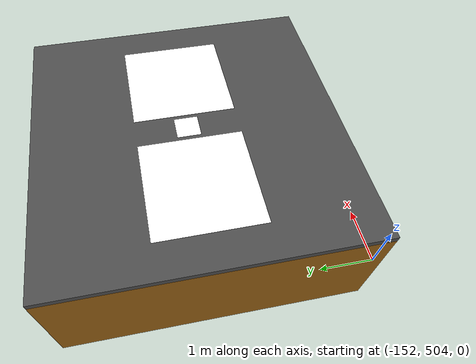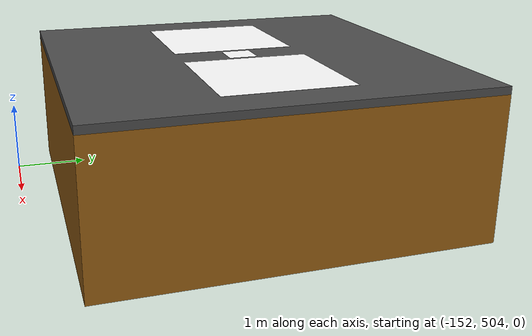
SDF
<sdf version="1.9">
 <world name="applepark_city_uav">
  <magnetic_field>6.0e-6 2.3e-5 -4.2e-5</magnetic_field>
  <atmosphere type="adiabatic"/>
  <plugin filename="gz-sim-physics-system" name="gz::sim::systems::Physics"/>
  <plugin filename="gz-sim-user-commands-system" name="gz::sim::systems::UserCommands"/>
  <plugin filename="gz-sim-scene-broadcaster-system" name="gz::sim::systems::SceneBroadcaster"/>
  <plugin filename="gz-sim-contact-system" name="gz::sim::systems::Contact"/>
  <plugin filename="gz-sim-sensors-system" name="gz::sim::systems::Sensors">
   <render_engine>ogre2</render_engine>
  </plugin>
  <plugin filename="gz-sim-imu-system" name="gz::sim::systems::Imu"/>
  <plugin filename="gz-sim-air-pressure-system" name="gz::sim::systems::AirPressure"/>
  <plugin filename="gz-sim-magnetometer-system" name="gz::sim::systems::Magnetometer"/>
  <plugin filename="gz-sim-navsat-system" name="gz::sim::systems::NavSat"/>
  <physics name="2ms" type="ignored">
   <max_step_size>0.002</max_step_size>
   <real_time_factor>1</real_time_factor>
   <real_time_update_rate>500</real_time_update_rate>
  </physics>
  <gravity>0 0 -9.8066</gravity>
  <scene><ambient>0.45 0.48 0.55 1</ambient><grid>false</grid><origin_visual>false</origin_visual></scene>
  <light type="directional" name="sun">
   <pose>0 -7000 7000 0 0 0</pose>
   <diffuse>0.9 0.88 0.82 1</diffuse>
   <specular>0 0 0 1</specular>
   <direction>0 0.6 -0.6</direction>
  </light>
  <spherical_coordinates>
   <surface_model>EARTH_WGS84</surface_model>
   <latitude_deg>37.32977431415926</latitude_deg>
   <longitude_deg>-121.99860517699835</longitude_deg>
   <elevation>50.6</elevation>
  </spherical_coordinates>
  <model name="applepark_uav_buildings">
   <static>true</static>
   <link name="buildings">
    <visual name="buildings_visual">
     <geometry><mesh><uri>mesh/buildings_uav.dae</uri><scale>1 1 1</scale></mesh></geometry>
    </visual>
    <collision name="building_001_exact_polyline">
     <pose>0 0 -0.05 0 0 0</pose>
     <geometry>
      <polyline>
       <height>48.2852941176</height>
       <point>-363.344 356.3635</point>
       <point>-327.687 342.1635</point>
       <point>-318.774 363.467</point>
       <point>-354.431 378.259</point>
      </polyline>
     </geometry>
    </collision>
    <collision name="building_002_exact_polyline">
     <pose>0 0 -0.05 0 0 0</pose>
     <geometry>
      <polyline>
       <height>30.1970588235</height>
       <point>-340.76375 397.7875</point>
       <point>-312.23825 386.54575</point>
       <point>-304.51375 405.48225</point>
       <point>-333.03925 416.724</point>
      </polyline>
     </geometry>
    </collision>
    <collision name="building_004_exact_polyline">
     <pose>0 0 -0.05 0 0 0</pose>
     <geometry>
      <polyline>
       <height>23.1382352941</height>
       <point>-604.0315 538.0205</point>
       <point>-585.0145 528.55325</point>
       <point>-575.507 548.0815</point>
       <point>-594.524 557.54875</point>
      </polyline>
     </geometry>
    </collision>
    <collision name="building_005_exact_polyline">
     <pose>0 0 -0.05 0 0 0</pose>
     <geometry>
      <polyline>
       <height>33.5794117647</height>
       <point>551.222 552.3005</point>
       <point>551.22375 535.13975</point>
       <point>591.03975 535.1435</point>
       <point>591.038 551.7125</point>
      </polyline>
     </geometry>
    </collision>
    <collision name="building_007_exact_polyline">
     <pose>0 0 -0.05 0 0 0</pose>
     <geometry>
      <polyline>
       <height>38.4323529412</height>
       <point>418.102 602.58725</point>
       <point>418.10325 587.7935</point>
       <point>490.60375 587.8</point>
       <point>490.60225 602.59375</point>
      </polyline>
     </geometry>
    </collision>
    <collision name="building_009_exact_polyline">
     <pose>0 0 -0.05 0 0 0</pose>
     <geometry>
      <polyline>
       <height>34.4617647059</height>
       <point>-284.85 -553.74675</point>
       <point>-283.65875 -599.9035</point>
       <point>-242.058 -599.30925</point>
       <point>-242.655 -552.561</point>
      </polyline>
     </geometry>
    </collision>
    <collision name="building_010_exact_polyline">
     <pose>0 0 -0.05 0 0 0</pose>
     <geometry>
      <polyline>
       <height>46.9617647059</height>
       <point>387.8525 -61.953</point>
       <point>387.85575 -101.6005</point>
       <point>430.64425 -101.005</point>
       <point>430.64075 -61.94925</point>
      </polyline>
     </geometry>
    </collision>
    <collision name="building_011_exact_polyline">
     <pose>0 0 -0.05 0 0 0</pose>
     <geometry>
      <polyline>
       <height>29.3147058824</height>
       <point>509.0485 343.99975</point>
       <point>520.93425 342.81725</point>
       <point>520.934 344.00075</point>
       <point>532.22525 342.8185</point>
       <point>535.78775 377.14025</point>
       <point>513.20525 379.50525</point>
      </polyline>
     </geometry>
    </collision>
    <collision name="building_012_exact_polyline">
     <pose>0 0 -0.05 0 0 0</pose>
     <geometry>
      <polyline>
       <height>25.7852941176</height>
       <point>433.5875 214.39925</point>
       <point>433.58875 201.3805</point>
       <point>469.8395 201.38375</point>
       <point>470.43175 223.27875</point>
       <point>435.3695 223.2755</point>
       <point>435.3705 214.39925</point>
      </polyline>
     </geometry>
    </collision>
    <collision name="building_014_exact_polyline">
     <pose>0 0 -0.05 0 0 0</pose>
     <geometry>
      <polyline>
       <height>41.9617647059</height>
       <point>551.2455 305.53975</point>
       <point>552.4355 290.74625</point>
       <point>553.624 290.74625</point>
       <point>553.62475 283.64525</point>
       <point>588.68675 286.60725</point>
       <point>586.90175 308.502</point>
      </polyline>
     </geometry>
    </collision>
    <collision name="building_015_exact_polyline">
     <pose>0 0 -0.05 0 0 0</pose>
     <geometry>
      <polyline>
       <height>34.1676470588</height>
       <point>-92.893 -533.61575</point>
       <point>-73.281 -535.38975</point>
       <point>-72.68725 -527.10525</point>
       <point>-64.9615 -527.6965</point>
       <point>-64.36775 -517.045</point>
       <point>-91.70575 -514.67975</point>
      </polyline>
     </geometry>
    </collision>
    <collision name="building_018_exact_polyline">
     <pose>0 0 -0.05 0 0 0</pose>
     <geometry>
      <polyline>
       <height>20.6382352941</height>
       <point>-605.80725 364.04525</point>
       <point>-590.3555 345.11</point>
       <point>-602.2405 335.64125</point>
       <point>-590.3545 321.43975</point>
       <point>-559.4535 347.47825</point>
       <point>-586.79125 380.0235</point>
      </polyline>
     </geometry>
    </collision>
    <collision name="building_019_exact_polyline">
     <pose>0 0 -0.05 0 0 0</pose>
     <geometry>
      <polyline>
       <height>29.6088235294</height>
       <point>459.12925 349.91275</point>
       <point>471.01475 348.73025</point>
       <point>471.0145 349.91375</point>
       <point>480.523 348.73125</point>
       <point>484.67975 383.05325</point>
       <point>463.28575 385.41825</point>
      </polyline>
     </geometry>
    </collision>
    <collision name="building_020_exact_polyline">
     <pose>0 0 -0.05 0 0 0</pose>
     <geometry>
      <polyline>
       <height>27.8441176471</height>
       <point>432.99475 197.23825</point>
       <point>432.99675 175.3435</point>
       <point>472.219 175.347</point>
       <point>472.218 185.9985</point>
       <point>471.0295 185.9985</point>
       <point>471.0285 197.24175</point>
      </polyline>
     </geometry>
    </collision>
    <collision name="building_022_exact_polyline">
     <pose>0 0 -0.05 0 0 0</pose>
     <geometry>
      <polyline>
       <height>44.9029411765</height>
       <point>547.1245 -104.54475</point>
       <point>547.12625 -122.889</point>
       <point>587.53775 -122.88525</point>
       <point>587.53325 -77.32025</point>
       <point>563.16775 -77.32275</point>
       <point>563.17025 -104.54325</point>
      </polyline>
     </geometry>
    </collision>
    <collision name="building_026_exact_polyline">
     <pose>0 0 -0.05 0 0 0</pose>
     <geometry>
      <polyline>
       <height>46.3735294118</height>
       <point>437.79875 -357.233</point>
       <point>438.39675 -398.06375</point>
       <point>480.5915 -397.46825</point>
       <point>479.99475 -371.43125</point>
       <point>456.223 -372.025</point>
       <point>455.6275 -357.23125</point>
      </polyline>
     </geometry>
    </collision>
    <collision name="building_027_exact_polyline">
     <pose>0 0 -0.05 0 0 0</pose>
     <geometry>
      <polyline>
       <height>42.9911764706</height>
       <point>-283.668 -433.62125</point>
       <point>-283.667 -451.9655</point>
       <point>-243.84925 -451.96325</point>
       <point>-243.25725 -409.94875</point>
       <point>-268.812 -409.95025</point>
       <point>-268.81075 -433.62025</point>
      </polyline>
     </geometry>
    </collision>
    <collision name="building_028_exact_polyline">
     <pose>0 0 -0.05 0 0 0</pose>
     <geometry>
      <polyline>
       <height>38.1382352941</height>
       <point>-397.178 -437.76925</point>
       <point>-396.58175 -480.3755</point>
       <point>-371.62125 -479.7825</point>
       <point>-371.6225 -454.929</point>
       <point>-355.5765 -454.928</point>
       <point>-356.17175 -437.1755</point>
      </polyline>
     </geometry>
    </collision>
    <collision name="building_031_exact_polyline">
     <pose>0 0 -0.05 0 0 0</pose>
     <geometry>
      <polyline>
       <height>42.1088235294</height>
       <point>137.687 -436.5525</point>
       <point>138.28425 -476.19975</point>
       <point>154.9245 -476.1985</point>
       <point>155.51775 -461.40475</point>
       <point>179.2895 -461.9945</point>
       <point>179.882 -437.141</point>
      </polyline>
     </geometry>
    </collision>
    <collision name="building_032_exact_polyline">
     <pose>0 0 -0.05 0 0 0</pose>
     <geometry>
      <polyline>
       <height>47.1088235294</height>
       <point>188.7525 126.79925</point>
       <point>189.3485 105.49625</point>
       <point>214.30825 105.49825</point>
       <point>214.30775 110.824</point>
       <point>228.5705 110.82525</point>
       <point>228.56925 126.8025</point>
      </polyline>
     </geometry>
    </collision>
    <collision name="building_033_exact_polyline">
     <pose>0 0 -0.05 0 0 0</pose>
     <geometry>
      <polyline>
       <height>45.3441176471</height>
       <point>189.982 -398.67625</point>
       <point>235.14825 -399.2645</point>
       <point>235.145 -358.43375</point>
       <point>214.93925 -358.43525</point>
       <point>214.346 -373.82075</point>
       <point>190.57425 -373.231</point>
      </polyline>
     </geometry>
    </collision>
    <collision name="building_034_exact_polyline">
     <pose>0 0 -0.05 0 0 0</pose>
     <geometry>
      <polyline>
       <height>43.8735294118</height>
       <point>88.9315 -115.8265</point>
       <point>88.93275 -134.17075</point>
       <point>128.15575 -134.75975</point>
       <point>128.1525 -92.1535</point>
       <point>103.78675 -92.15525</point>
       <point>89.524 -91.5645</point>
      </polyline>
     </geometry>
    </collision>
    <collision name="building_036_exact_polyline">
     <pose>0 0 -0.05 0 0 0</pose>
     <geometry>
      <polyline>
       <height>25.9323529412</height>
       <point>-99.44875 -244.2495</point>
       <point>-99.4475 -263.1855</point>
       <point>-82.21325 -263.1845</point>
       <point>-82.2115 -288.62975</point>
       <point>-59.03425 -288.62825</point>
       <point>-58.44275 -244.83875</point>
      </polyline>
     </geometry>
    </collision>
    <collision name="building_038_exact_polyline">
     <pose>0 0 -0.05 0 0 0</pose>
     <geometry>
      <polyline>
       <height>25.3441176471</height>
       <point>-208.798 -243.07275</point>
       <point>-208.7955 -288.046</point>
       <point>-187.401 -288.04475</point>
       <point>-187.40275 -257.86525</point>
       <point>-167.79125 -257.864</point>
       <point>-167.79225 -243.07025</point>
      </polyline>
     </geometry>
    </collision>
    <collision name="building_040_exact_polyline">
     <pose>0 0 -0.05 0 0 0</pose>
     <geometry>
      <polyline>
       <height>36.8147058824</height>
       <point>-396.60125 -86.8605</point>
       <point>-396.59925 -125.916</point>
       <point>-358.565 -126.50575</point>
       <point>-357.973 -82.71625</point>
       <point>-387.093 -82.126</point>
       <point>-387.09275 -86.86</point>
      </polyline>
     </geometry>
    </collision>
    <collision name="building_042_exact_polyline">
     <pose>0 0 -0.05 0 0 0</pose>
     <geometry>
      <polyline>
       <height>49.6088235294</height>
       <point>295.1245 175.92325</point>
       <point>295.12575 159.946</point>
       <point>309.98275 159.94725</point>
       <point>309.985 133.3185</point>
       <point>334.35025 133.3205</point>
       <point>334.34675 175.33475</point>
      </polyline>
     </geometry>
    </collision>
    <collision name="building_043_exact_polyline">
     <pose>0 0 -0.05 0 0 0</pose>
     <geometry>
      <polyline>
       <height>36.0794117647</height>
       <point>-220.717 325.60025</point>
       <point>-207.64275 320.867</point>
       <point>-215.961 297.78825</point>
       <point>-193.37825 289.505</point>
       <point>-184.4655 313.17575</point>
       <point>-178.52375 329.745</point>
       <point>-214.77525 342.7615</point>
      </polyline>
     </geometry>
    </collision>
    <collision name="building_045_exact_polyline">
     <pose>0 0 -0.05 0 0 0</pose>
     <geometry>
      <polyline>
       <height>43.4323529412</height>
       <point>-21.0025 -247.20325</point>
       <point>-20.40525 -288.62575</point>
       <point>4.55475 -288.624</point>
       <point>3.959 -264.36225</point>
       <point>20.00475 -264.36125</point>
       <point>19.409 -242.46625</point>
       <point>-1.9855 -242.46775</point>
       <point>-1.98525 -247.20175</point>
      </polyline>
     </geometry>
    </collision>
    <collision name="building_046_exact_polyline">
     <pose>0 0 -0.05 0 0 0</pose>
     <geometry>
      <polyline>
       <height>26.9617647059</height>
       <point>-17.42925 -357.8605</point>
       <point>-17.426 -403.4255</point>
       <point>20.01425 -402.831</point>
       <point>20.013 -384.48675</point>
       <point>6.9385 -384.48775</point>
       <point>6.93825 -377.9785</point>
       <point>5.15525 -377.9785</point>
       <point>5.154 -357.859</point>
      </polyline>
     </geometry>
    </collision>
    <collision name="building_047_exact_polyline">
     <pose>0 0 -0.05 0 0 0</pose>
     <geometry>
      <polyline>
       <height>39.3147058824</height>
       <point>554.816 255.24125</point>
       <point>555.41125 244.58975</point>
       <point>557.194 244.59</point>
       <point>557.7895 233.34675</point>
       <point>567.29775 233.93925</point>
       <point>567.29775 235.12275</point>
       <point>592.85125 236.9005</point>
       <point>591.0665 258.2035</point>
      </polyline>
     </geometry>
    </collision>
    <collision name="building_048_exact_polyline">
     <pose>0 0 -0.05 0 0 0</pose>
     <geometry>
      <polyline>
       <height>49.4617647059</height>
       <point>178.072 -84.457</point>
       <point>206.59975 -111.67525</point>
       <point>219.07875 -99.2475</point>
       <point>208.975 -89.1885</point>
       <point>213.729 -84.45425</point>
       <point>211.946 -82.679</point>
       <point>225.019 -68.476</point>
       <point>208.97225 -52.5</point>
      </polyline>
     </geometry>
    </collision>
    <collision name="building_049_exact_polyline">
     <pose>0 0 -0.05 0 0 0</pose>
     <geometry>
      <polyline>
       <height>21.6676470588</height>
       <point>295.12425 178.882</point>
       <point>347.4205 178.8865</point>
       <point>347.419 197.23075</point>
       <point>334.93925 197.22975</point>
       <point>335.53125 223.85875</point>
       <point>309.383 223.8565</point>
       <point>309.38525 197.2275</point>
       <point>295.717 197.2265</point>
      </polyline>
     </geometry>
    </collision>
    <collision name="building_050_exact_polyline">
     <pose>0 0 -0.05 0 0 0</pose>
     <geometry>
      <polyline>
       <height>37.1088235294</height>
       <point>485.27975 322.6945</point>
       <point>485.28175 300.79975</point>
       <point>520.938 300.21125</point>
       <point>520.937 310.86275</point>
       <point>522.72 310.863</point>
       <point>522.71875 322.698</point>
       <point>499.54225 323.2875</point>
       <point>499.54225 322.104</point>
      </polyline>
     </geometry>
    </collision>
    <collision name="building_051_exact_polyline">
     <pose>0 0 -0.05 0 0 0</pose>
     <geometry>
      <polyline>
       <height>43.7264705882</height>
       <point>487.07025 236.8905</point>
       <point>487.07125 225.64725</point>
       <point>523.32225 225.059</point>
       <point>523.3215 232.75175</point>
       <point>525.10425 232.75175</point>
       <point>525.103 246.954</point>
       <point>488.258 247.54225</point>
       <point>488.259 236.89075</point>
      </polyline>
     </geometry>
    </collision>
    <collision name="building_053_exact_polyline">
     <pose>0 0 -0.05 0 0 0</pose>
     <geometry>
      <polyline>
       <height>38.5794117647</height>
       <point>488.8475 298.433</point>
       <point>488.8495 276.53825</point>
       <point>525.6945 275.94975</point>
       <point>525.6935 287.193</point>
       <point>523.91075 287.193</point>
       <point>524.50425 294.294</point>
       <point>523.31575 294.294</point>
       <point>523.90975 297.8445</point>
      </polyline>
     </geometry>
    </collision>
    <collision name="building_054_exact_polyline">
     <pose>0 0 -0.05 0 0 0</pose>
     <geometry>
      <polyline>
       <height>21.5205882353</height>
       <point>-154.1575 311.40225</point>
       <point>-139.89375 293.05875</point>
       <point>-107.21025 317.9145</point>
       <point>-114.34225 326.79025</point>
       <point>-103.0515 335.0755</point>
       <point>-117.9095 354.60225</point>
       <point>-132.1715 343.95</point>
       <point>-124.44525 333.89075</point>
      </polyline>
     </geometry>
    </collision>
    <collision name="building_055_exact_polyline">
     <pose>0 0 -0.05 0 0 0</pose>
     <geometry>
      <polyline>
       <height>36.6676470588</height>
       <point>-608.174 101.899</point>
       <point>-601.041 59.29325</point>
       <point>-583.21275 62.8445</point>
       <point>-580.2405 45.68375</point>
       <point>-559.441 49.235</point>
       <point>-565.9795 85.33175</point>
       <point>-584.99625 82.37225</point>
       <point>-589.15725 105.45025</point>
      </polyline>
     </geometry>
    </collision>
    <collision name="building_056_exact_polyline">
     <pose>0 0 -0.05 0 0 0</pose>
     <geometry>
      <polyline>
       <height>38.2852941176</height>
       <point>-185.06625 420.8745</point>
       <point>-143.4665 406.08325</point>
       <point>-129.8005 443.3645</point>
       <point>-147.629 449.28075</point>
       <point>-152.38225 435.67025</point>
       <point>-157.73075 437.44525</point>
       <point>-158.91925 435.07825</point>
       <point>-177.342 441.58625</point>
      </polyline>
     </geometry>
    </collision>
    <collision name="building_057_exact_polyline">
     <pose>0 0 -0.05 0 0 0</pose>
     <geometry>
      <polyline>
       <height>44.3147058824</height>
       <point>-108.344 -544.86</point>
       <point>-84.57025 -572.671</point>
       <point>-47.726 -541.30575</point>
       <point>-60.20725 -526.51275</point>
       <point>-78.035 -541.8995</point>
       <point>-79.818 -540.716</point>
       <point>-84.57225 -544.8585</point>
       <point>-94.676 -533.02425</point>
      </polyline>
     </geometry>
    </collision>
    <collision name="building_058_exact_polyline">
     <pose>0 0 -0.05 0 0 0</pose>
     <geometry>
      <polyline>
       <height>41.2264705882</height>
       <point>-449.5025 122.0255</point>
       <point>-449.50125 96.58025</point>
       <point>-407.30725 95.9905</point>
       <point>-407.30825 115.51825</point>
       <point>-405.5255 115.51825</point>
       <point>-404.93225 135.638</point>
       <point>-424.5435 136.22875</point>
       <point>-424.54275 122.02675</point>
      </polyline>
     </geometry>
    </collision>
    <collision name="building_059_exact_polyline">
     <pose>0 0 -0.05 0 0 0</pose>
     <geometry>
      <polyline>
       <height>40.3441176471</height>
       <point>-296.19725 464.066</point>
       <point>-255.786 446.9075</point>
       <point>-246.873 468.211</point>
       <point>-263.513 475.31125</point>
       <point>-262.91875 477.67825</point>
       <point>-269.456 480.6365</point>
       <point>-263.514 494.839</point>
       <point>-279.55975 501.939</point>
      </polyline>
     </geometry>
    </collision>
    <collision name="building_060_exact_polyline">
     <pose>0 0 -0.05 0 0 0</pose>
     <geometry>
      <polyline>
       <height>37.55</height>
       <point>-561.2335 280.01825</point>
       <point>-552.31875 264.63325</point>
       <point>-539.245 272.91825</point>
       <point>-527.35875 253.391</point>
       <point>-493.486 274.10375</point>
       <point>-502.995 289.489</point>
       <point>-515.4745 281.7955</point>
       <point>-527.36075 300.731</point>
      </polyline>
     </geometry>
    </collision>
    <collision name="building_062_exact_polyline">
     <pose>0 0 -0.05 0 0 0</pose>
     <geometry>
      <polyline>
       <height>31.3735294118</height>
       <point>547.127 -130.58175</point>
       <point>547.129 -150.7015</point>
       <point>559.609 -150.70025</point>
       <point>559.6115 -177.329</point>
       <point>585.16575 -177.32675</point>
       <point>585.1615 -132.3535</point>
       <point>563.173 -132.3555</point>
       <point>563.17275 -130.58025</point>
      </polyline>
     </geometry>
    </collision>
    <collision name="building_063_exact_polyline">
     <pose>0 0 -0.05 0 0 0</pose>
     <geometry>
      <polyline>
       <height>42.4029411765</height>
       <point>-479.199 -255.51375</point>
       <point>-478.604 -275.0415</point>
       <point>-459.5865 -275.0405</point>
       <point>-459.58675 -273.857</point>
       <point>-439.975 -273.2645</point>
       <point>-441.16575 -230.65825</point>
       <point>-466.12575 -231.25125</point>
       <point>-465.5305 -255.513</point>
      </polyline>
     </geometry>
    </collision>
    <collision name="building_064_exact_polyline">
     <pose>0 0 -0.05 0 0 0</pose>
     <geometry>
      <polyline>
       <height>39.4617647059</height>
       <point>-592.7075 -274.45475</point>
       <point>-592.70575 -320.0195</point>
       <point>-573.6885 -320.01875</point>
       <point>-573.68925 -302.26625</point>
       <point>-562.39775 -302.26575</point>
       <point>-562.39775 -300.4905</point>
       <point>-546.94625 -300.48975</point>
       <point>-546.94725 -274.45275</point>
      </polyline>
     </geometry>
    </collision>
    <collision name="building_065_exact_polyline">
     <pose>0 0 -0.05 0 0 0</pose>
     <geometry>
      <polyline>
       <height>48.5794117647</height>
       <point>435.388 16.16225</point>
       <point>435.39175 -24.6685</point>
       <point>480.55725 -24.6645</point>
       <point>480.55525 -1.58625</point>
       <point>460.3495 -1.588</point>
       <point>460.34925 1.37075</point>
       <point>453.81225 1.37025</point>
       <point>453.81075 16.164</point>
      </polyline>
     </geometry>
    </collision>
    <collision name="building_067_exact_polyline">
     <pose>0 0 -0.05 0 0 0</pose>
     <geometry>
      <polyline>
       <height>43.1382352941</height>
       <point>436.00225 -206.928</point>
       <point>482.357 -208.1075</point>
       <point>482.949 -185.029</point>
       <point>463.3375 -184.439</point>
       <point>463.33725 -182.072</point>
       <point>455.6115 -181.481</point>
       <point>455.61025 -166.68725</point>
       <point>437.18725 -166.097</point>
      </polyline>
     </geometry>
    </collision>
    <collision name="building_069_exact_polyline">
     <pose>0 0 -0.05 0 0 0</pose>
     <geometry>
      <polyline>
       <height>26.3735294118</height>
       <point>-285.46625 -153.7225</point>
       <point>-271.2035 -153.72175</point>
       <point>-271.796 -184.493</point>
       <point>-246.836 -184.4915</point>
       <point>-246.83825 -142.477</point>
       <point>-265.26125 -142.47825</point>
       <point>-265.2615 -136.56075</point>
       <point>-284.873 -136.56175</point>
      </polyline>
     </geometry>
    </collision>
    <collision name="building_070_exact_polyline">
     <pose>0 0 -0.05 0 0 0</pose>
     <geometry>
      <polyline>
       <height>36.3735294118</height>
       <point>-19.24 55.774</point>
       <point>20.57675 53.40975</point>
       <point>21.76425 69.97875</point>
       <point>6.313 71.16125</point>
       <point>6.3125 77.07875</point>
       <point>3.93525 77.07875</point>
       <point>5.1225 98.38175</point>
       <point>-16.27175 99.56375</point>
      </polyline>
     </geometry>
    </collision>
    <collision name="building_072_exact_polyline">
     <pose>0 0 -0.05 0 0 0</pose>
     <geometry>
      <polyline>
       <height>24.3147058824</height>
       <point>-284.2875 24.39475</point>
       <point>-243.87625 21.43825</point>
       <point>-240.9075 66.41175</point>
       <point>-263.49025 68.18575</point>
       <point>-265.272 48.65775</point>
       <point>-267.05475 48.65775</point>
       <point>-267.6485 41.5565</point>
       <point>-283.1 42.73925</point>
      </polyline>
     </geometry>
    </collision>
    <collision name="building_073_exact_polyline">
     <pose>0 0 -0.05 0 0 0</pose>
     <geometry>
      <polyline>
       <height>45.7852941176</height>
       <point>362.2625 352.27125</point>
       <point>364.0455 352.27125</point>
       <point>364.0465 340.43625</point>
       <point>401.4855 339.84775</point>
       <point>401.485 347.5405</point>
       <point>402.07925 347.5405</point>
       <point>402.67225 362.92625</point>
       <point>362.856 362.92275</point>
      </polyline>
     </geometry>
    </collision>
    <collision name="building_074_exact_polyline">
     <pose>0 0 -0.05 0 0 0</pose>
     <geometry>
      <polyline>
       <height>46.0794117647</height>
       <point>-207.6215 -37.143</point>
       <point>-207.61925 -79.1575</point>
       <point>-184.442 -79.156</point>
       <point>-184.442 -80.93125</point>
       <point>-168.39625 -80.93025</point>
       <point>-168.3975 -61.4025</point>
       <point>-182.066 -61.40325</point>
       <point>-182.0675 -37.1415</point>
      </polyline>
     </geometry>
    </collision>
    <collision name="building_076_exact_polyline">
     <pose>0 0 -0.05 0 0 0</pose>
     <geometry>
      <polyline>
       <height>44.7558823529</height>
       <point>363.46025 245.75575</point>
       <point>364.64875 245.756</point>
       <point>364.0555 233.92075</point>
       <point>400.90075 233.33225</point>
       <point>400.89975 243.392</point>
       <point>402.08825 243.39225</point>
       <point>402.08725 257.0025</point>
       <point>364.0535 256.99925</point>
      </polyline>
     </geometry>
    </collision>
    <collision name="building_078_exact_polyline">
     <pose>0 0 -0.05 0 0 0</pose>
     <geometry>
      <polyline>
       <height>39.0205882353</height>
       <point>135.90125 -399.27225</point>
       <point>181.662 -399.26875</point>
       <point>181.66025 -376.78225</point>
       <point>161.45425 -376.78375</point>
       <point>161.454 -374.41675</point>
       <point>154.91675 -374.41725</point>
       <point>154.9155 -358.44</point>
       <point>136.4925 -358.44125</point>
      </polyline>
     </geometry>
    </collision>
    <collision name="building_082_exact_polyline">
     <pose>0 0 -0.05 0 0 0</pose>
     <geometry>
      <polyline>
       <height>32.9911764706</height>
       <point>139.41075 348.111</point>
       <point>164.96475 345.154</point>
       <point>164.37075 341.01175</point>
       <point>181.60475 338.646</point>
       <point>186.94975 383.61975</point>
       <point>168.52725 385.98525</point>
       <point>166.7455 371.19125</point>
       <point>142.38025 374.14825</point>
      </polyline>
     </geometry>
    </collision>
    <collision name="building_083_exact_polyline">
     <pose>0 0 -0.05 0 0 0</pose>
     <geometry>
      <polyline>
       <height>21.9617647059</height>
       <point>64.00525 -586.271</point>
       <point>109.76625 -586.26775</point>
       <point>110.3575 -544.845</point>
       <point>91.34 -544.8465</point>
       <point>90.74675 -559.64025</point>
       <point>84.80375 -559.64075</point>
       <point>84.804 -563.19125</point>
       <point>64.59775 -563.19275</point>
      </polyline>
     </geometry>
    </collision>
    <collision name="building_084_exact_polyline">
     <pose>0 0 -0.05 0 0 0</pose>
     <geometry>
      <polyline>
       <height>33.7264705882</height>
       <point>-159.451 -589.24475</point>
       <point>-117.2555 -592.20075</point>
       <point>-114.2865 -553.145</point>
       <point>-132.1155 -551.9625</point>
       <point>-133.30325 -567.94</point>
       <point>-139.24625 -567.3485</point>
       <point>-139.246 -569.7155</point>
       <point>-158.26375 -568.53325</point>
      </polyline>
     </geometry>
    </collision>
    <collision name="building_086_exact_polyline">
     <pose>0 0 -0.05 0 0 0</pose>
     <geometry>
      <polyline>
       <height>42.8441176471</height>
       <point>-536.272 235.04625</point>
       <point>-529.73425 217.88575</point>
       <point>-515.47175 223.212</point>
       <point>-512.5 215.5195</point>
       <point>-510.71725 216.703</point>
       <point>-503.58525 198.359</point>
       <point>-482.786 206.6445</point>
       <point>-498.83325 249.25</point>
      </polyline>
     </geometry>
    </collision>
    <collision name="building_087_exact_polyline">
     <pose>0 0 -0.05 0 0 0</pose>
     <geometry>
      <polyline>
       <height>37.9911764706</height>
       <point>300.45575 383.037</point>
       <point>300.45975 333.32975</point>
       <point>324.825 333.332</point>
       <point>324.82475 336.8825</point>
       <point>344.43575 336.884</point>
       <point>344.434 356.412</point>
       <point>326.606 356.41025</point>
       <point>326.60375 382.4475</point>
      </polyline>
     </geometry>
    </collision>
    <collision name="building_088_exact_polyline">
     <pose>0 0 -0.05 0 0 0</pose>
     <geometry>
      <polyline>
       <height>49.0205882353</height>
       <point>-114.35725 564.083</point>
       <point>-87.02025 554.6165</point>
       <point>-92.36775 539.23075</point>
       <point>-75.72775 533.31425</point>
       <point>-57.309 584.798</point>
       <point>-76.32575 591.306</point>
       <point>-81.079 577.69525</point>
       <point>-106.633 586.57</point>
      </polyline>
     </geometry>
    </collision>
    <collision name="building_089_exact_polyline">
     <pose>0 0 -0.05 0 0 0</pose>
     <geometry>
      <polyline>
       <height>48.1382352941</height>
       <point>344.41625 565.89225</point>
       <point>345.01725 486.5975</point>
       <point>377.702 487.192</point>
       <point>377.70025 506.128</point>
       <point>379.483 506.12825</point>
       <point>379.47975 545.7755</point>
       <point>377.1025 545.7755</point>
       <point>377.10075 566.48675</point>
      </polyline>
     </geometry>
    </collision>
    <collision name="building_090_exact_polyline">
     <pose>0 0 -0.05 0 0 0</pose>
     <geometry>
      <polyline>
       <height>29.7558823529</height>
       <point>192.89575 342.78925</point>
       <point>239.84325 341.6095</point>
       <point>240.43575 364.68775</point>
       <point>219.042 365.27775</point>
       <point>219.04175 367.64475</point>
       <point>213.099 367.6445</point>
       <point>213.69225 381.25475</point>
       <point>194.08125 381.845</point>
      </polyline>
     </geometry>
    </collision>
    <collision name="building_091_exact_polyline">
     <pose>0 0 -0.05 0 0 0</pose>
     <geometry>
      <polyline>
       <height>40.9323529412</height>
       <point>-186.83425 174.7055</point>
       <point>-147.01725 167.015</point>
       <point>-143.45275 184.768</point>
       <point>-158.30975 187.72575</point>
       <point>-157.12175 194.235</point>
       <point>-159.49875 194.82675</point>
       <point>-155.34 214.35475</point>
       <point>-177.92275 219.0875</point>
      </polyline>
     </geometry>
    </collision>
    <collision name="building_092_exact_polyline">
     <pose>0 0 -0.05 0 0 0</pose>
     <geometry>
      <polyline>
       <height>47.4029411765</height>
       <point>-376.41025 201.32375</point>
       <point>-359.176 198.95775</point>
       <point>-356.79975 214.3435</point>
       <point>-330.65125 210.79425</point>
       <point>-327.087 236.23975</point>
       <point>-371.658 242.155</point>
       <point>-375.22225 216.11775</point>
       <point>-374.628 216.11775</point>
      </polyline>
     </geometry>
    </collision>
    <collision name="building_093_exact_polyline">
     <pose>0 0 -0.05 0 0 0</pose>
     <geometry>
      <polyline>
       <height>22.2558823529</height>
       <point>-71.54525 184.18075</point>
       <point>-26.97375 175.3075</point>
       <point>-18.65675 215.547</point>
       <point>-36.48525 219.0965</point>
       <point>-40.04975 203.7105</point>
       <point>-48.36975 205.48525</point>
       <point>-48.964 203.11825</point>
       <point>-67.38675 206.6675</point>
      </polyline>
     </geometry>
    </collision>
    <collision name="building_095_exact_polyline">
     <pose>0 0 -0.05 0 0 0</pose>
     <geometry>
      <polyline>
       <height>28.7264705882</height>
       <point>237.52525 -396.89725</point>
       <point>281.503 -397.4855</point>
       <point>281.50125 -374.999</point>
       <point>263.6725 -375.0005</point>
       <point>263.67225 -372.0415</point>
       <point>257.135 -372.04225</point>
       <point>257.72825 -358.43175</point>
       <point>238.1165 -358.4335</point>
      </polyline>
     </geometry>
    </collision>
    <collision name="building_097_exact_polyline">
     <pose>0 0 -0.05 0 0 0</pose>
     <geometry>
      <polyline>
       <height>20.4911764706</height>
       <point>238.702 -246.59225</point>
       <point>239.29925 -285.056</point>
       <point>257.128 -285.0545</point>
       <point>257.12675 -271.44425</point>
       <point>264.25825 -271.44375</point>
       <point>264.258 -268.485</point>
       <point>284.464 -268.48325</point>
       <point>284.462 -245.99675</point>
      </polyline>
     </geometry>
    </collision>
    <collision name="building_099_exact_polyline">
     <pose>0 0 -0.05 0 0 0</pose>
     <geometry>
      <polyline>
       <height>31.0794117647</height>
       <point>88.9385 -210.50675</point>
       <point>88.9395 -227.07575</point>
       <point>110.92825 -227.07425</point>
       <point>110.92825 -228.25775</point>
       <point>129.9455 -228.25625</point>
       <point>129.9425 -185.65025</point>
       <point>104.388 -185.652</point>
       <point>104.38975 -210.50575</point>
      </polyline>
     </geometry>
    </collision>
    <collision name="building_100_exact_polyline">
     <pose>0 0 -0.05 0 0 0</pose>
     <geometry>
      <polyline>
       <height>48.7264705882</height>
       <point>-100.654 16.12125</point>
       <point>-79.25975 14.34725</point>
       <point>-79.26 16.12275</point>
       <point>-60.24275 14.3485</point>
       <point>-56.08575 58.73025</point>
       <point>-81.04575 61.09575</point>
       <point>-83.421 33.875</point>
       <point>-98.8725 35.0575</point>
      </polyline>
     </geometry>
    </collision>
    <collision name="building_102_exact_polyline">
     <pose>0 0 -0.05 0 0 0</pose>
     <geometry>
      <polyline>
       <height>45.6382352941</height>
       <point>-99.4415 -359.0495</point>
       <point>-99.44025 -376.802</point>
       <point>-82.80025 -376.801</point>
       <point>-82.7995 -386.86075</point>
       <point>-99.43975 -386.86175</point>
       <point>-99.4385 -404.61425</point>
       <point>-57.838 -404.61175</point>
       <point>-57.841 -359.04675</point>
      </polyline>
     </geometry>
    </collision>
    <collision name="building_103_exact_polyline">
     <pose>0 0 -0.05 0 0 0</pose>
     <geometry>
      <polyline>
       <height>33.2852941176</height>
       <point>-98.8695 -8.73225</point>
       <point>-87.57825 -8.7315</point>
       <point>-87.5775 -18.1995</point>
       <point>-85.2005 -18.1995</point>
       <point>-85.7935 -37.1355</point>
       <point>-57.86225 -38.31725</point>
       <point>-56.6765 7.24775</point>
       <point>-98.2765 8.4285</point>
      </polyline>
     </geometry>
    </collision>
    <collision name="building_104_exact_polyline">
     <pose>0 0 -0.05 0 0 0</pose>
     <geometry>
      <polyline>
       <height>35.05</height>
       <point>-98.2495 -411.71525</point>
       <point>-98.24825 -430.0595</point>
       <point>-83.391 -430.6505</point>
       <point>-83.39025 -440.1185</point>
       <point>-80.41875 -440.11825</point>
       <point>-80.41775 -457.279</point>
       <point>-57.24025 -457.2775</point>
       <point>-57.24325 -411.7125</point>
      </polyline>
     </geometry>
    </collision>
    <collision name="building_105_exact_polyline">
     <pose>0 0 -0.05 0 0 0</pose>
     <geometry>
      <polyline>
       <height>34.6088235294</height>
       <point>-590.92725 -214.6875</point>
       <point>-546.94975 -215.2775</point>
       <point>-546.9505 -195.74975</point>
       <point>-560.025 -195.75025</point>
       <point>-560.02525 -189.241</point>
       <point>-550.5165 -189.2405</point>
       <point>-549.923 -170.3045</point>
       <point>-590.33475 -169.7145</point>
      </polyline>
     </geometry>
    </collision>
    <collision name="building_106_exact_polyline">
     <pose>0 0 -0.05 0 0 0</pose>
     <geometry>
      <polyline>
       <height>33.8735294118</height>
       <point>-286.6615 -31.82175</point>
       <point>-247.43875 -33.003</point>
       <point>-246.2525 8.41975</point>
       <point>-251.60125 8.4195</point>
       <point>-251.60125 9.603</point>
       <point>-259.92125 9.6025</point>
       <point>-259.3275 18.47875</point>
       <point>-285.47575 19.069</point>
      </polyline>
     </geometry>
    </collision>
    <collision name="building_108_exact_polyline">
     <pose>0 0 -0.05 0 0 0</pose>
     <geometry>
      <polyline>
       <height>29.0205882353</height>
       <point>-588.552 -162.61325</point>
       <point>-566.5635 -163.20425</point>
       <point>-566.56425 -144.268</point>
       <point>-562.9985 -144.268</point>
       <point>-562.999 -135.39175</point>
       <point>-546.95325 -134.79925</point>
       <point>-547.54825 -117.04675</point>
       <point>-587.95975 -117.64025</point>
      </polyline>
     </geometry>
    </collision>
    <collision name="building_109_exact_polyline">
     <pose>0 0 -0.05 0 0 0</pose>
     <geometry>
      <polyline>
       <height>21.3735294118</height>
       <point>-208.207 -188.03975</point>
       <point>-208.20425 -233.60475</point>
       <point>-185.027 -233.60325</point>
       <point>-185.02825 -214.66725</point>
       <point>-182.651 -214.667</point>
       <point>-182.6515 -206.3825</point>
       <point>-167.2 -206.38175</point>
       <point>-167.20125 -188.03725</point>
      </polyline>
     </geometry>
    </collision>
    <collision name="building_110_exact_polyline">
     <pose>0 0 -0.05 0 0 0</pose>
     <geometry>
      <polyline>
       <height>24.6088235294</height>
       <point>-208.21025 -134.19025</point>
       <point>-183.8445 -134.78075</point>
       <point>-183.84575 -114.06925</point>
       <point>-181.4685 -114.06925</point>
       <point>-181.469 -106.96825</point>
       <point>-168.39475 -107.55925</point>
       <point>-167.8015 -87.4395</point>
       <point>-207.0245 -86.85025</point>
      </polyline>
     </geometry>
    </collision>
    <collision name="building_111_exact_polyline">
     <pose>0 0 -0.05 0 0 0</pose>
     <geometry>
      <polyline>
       <height>38.7264705882</height>
       <point>-90.5565 98.3755</point>
       <point>-75.105 96.0095</point>
       <point>-76.29325 88.90825</point>
       <point>-73.32175 88.31675</point>
       <point>-76.88625 68.78875</point>
       <point>-54.30325 64.648</point>
       <point>-47.17475 109.6215</point>
       <point>-87.58625 116.12825</point>
      </polyline>
     </geometry>
    </collision>
    <collision name="building_113_exact_polyline">
     <pose>0 0 -0.05 0 0 0</pose>
     <geometry>
      <polyline>
       <height>24.7558823529</height>
       <point>295.1285 126.21625</point>
       <point>295.13 109.05525</point>
       <point>315.3355 109.057</point>
       <point>315.337 91.3045</point>
       <point>312.95975 91.30425</point>
       <point>312.9605 82.428</point>
       <point>335.54325 82.43</point>
       <point>335.5395 126.2195</point>
      </polyline>
     </geometry>
    </collision>
    <collision name="building_114_exact_polyline">
     <pose>0 0 -0.05 0 0 0</pose>
     <geometry>
      <polyline>
       <height>35.4911764706</height>
       <point>485.27725 349.32325</point>
       <point>489.43725 347.5485</point>
       <point>494.1915 346.95725</point>
       <point>497.163 346.36575</point>
       <point>499.54 346.36575</point>
       <point>501.91725 345.77425</point>
       <point>507.26525 348.14175</point>
       <point>510.828 381.28025</point>
       <point>488.83975 383.64525</point>
      </polyline>
     </geometry>
    </collision>
    <collision name="building_116_exact_polyline">
     <pose>0 0 -0.05 0 0 0</pose>
     <geometry>
      <polyline>
       <height>27.4029411765</height>
       <point>262.4975 -543.64975</point>
       <point>262.50075 -581.522</point>
       <point>269.63225 -581.52125</point>
       <point>269.633 -590.98925</point>
       <point>283.302 -590.98825</point>
       <point>283.30125 -582.112</point>
       <point>308.26175 -582.10975</point>
       <point>308.85275 -544.23775</point>
      </polyline>
     </geometry>
    </collision>
    <collision name="building_117_exact_polyline">
     <pose>0 0 -0.05 0 0 0</pose>
     <geometry>
      <polyline>
       <height>22.1088235294</height>
       <point>-267.65575 169.96675</point>
       <point>-252.2045 166.41725</point>
       <point>-253.3925 159.90775</point>
       <point>-250.42125 159.31625</point>
       <point>-254.58 140.97175</point>
       <point>-232.5915 135.64725</point>
       <point>-223.0855 178.25375</point>
       <point>-263.49675 187.12775</point>
      </polyline>
     </geometry>
    </collision>
    <collision name="building_118_exact_polyline">
     <pose>0 0 -0.05 0 0 0</pose>
     <geometry>
      <polyline>
       <height>40.4911764706</height>
       <point>188.7815 -244.821</point>
       <point>188.78325 -266.71575</point>
       <point>201.26325 -266.71475</point>
       <point>201.2635 -269.6735</point>
       <point>214.93225 -269.6725</point>
       <point>214.9335 -285.64975</point>
       <point>233.95075 -285.64825</point>
       <point>233.9475 -244.81725</point>
      </polyline>
     </geometry>
    </collision>
    <collision name="building_119_exact_polyline">
     <pose>0 0 -0.05 0 0 0</pose>
     <geometry>
      <polyline>
       <height>35.6382352941</height>
       <point>115.11175 -544.84475</point>
       <point>115.115 -586.26725</point>
       <point>159.6875 -586.85575</point>
       <point>160.2785 -544.84125</point>
       <point>141.261 -544.84275</point>
       <point>140.66775 -560.22825</point>
       <point>133.53625 -560.229</point>
       <point>133.535 -544.84325</point>
      </polyline>
     </geometry>
    </collision>
    <collision name="building_120_exact_polyline">
     <pose>0 0 -0.05 0 0 0</pose>
     <geometry>
      <polyline>
       <height>26.6676470588</height>
       <point>122.7765 277.69125</point>
       <point>163.782 268.22625</point>
       <point>173.8815 309.64975</point>
       <point>132.876 319.70625</point>
       <point>128.7175 301.36175</point>
       <point>144.16875 297.81225</point>
       <point>141.7925 288.344</point>
       <point>126.341 291.8935</point>
      </polyline>
     </geometry>
    </collision>
    <collision name="building_121_exact_polyline">
     <pose>0 0 -0.05 0 0 0</pose>
     <geometry>
      <polyline>
       <height>37.4029411765</height>
       <point>9.26975 280.64175</point>
       <point>24.72125 277.09225</point>
       <point>27.6915 291.88625</point>
       <point>32.44575 290.70325</point>
       <point>32.44575 293.07025</point>
       <point>54.434 288.9295</point>
       <point>59.1865 312.00825</point>
       <point>16.99275 320.28975</point>
      </polyline>
     </geometry>
    </collision>
    <collision name="building_124_exact_polyline">
     <pose>0 0 -0.05 0 0 0</pose>
     <geometry>
      <polyline>
       <height>22.4029411765</height>
       <point>87.76775 -457.85925</point>
       <point>108.56825 -458.4495</point>
       <point>108.5685 -461.40825</point>
       <point>115.10575 -461.40775</point>
       <point>115.10675 -476.79325</point>
       <point>132.93575 -477.38375</point>
       <point>133.527 -437.1445</point>
       <point>88.3605 -435.96425</point>
      </polyline>
     </geometry>
    </collision>
    <collision name="building_125_exact_polyline">
     <pose>0 0 -0.05 0 0 0</pose>
     <geometry>
      <polyline>
       <height>30.05</height>
       <point>87.739 -60.79375</point>
       <point>103.19025 -60.7925</point>
       <point>103.19075 -67.8935</point>
       <point>87.7395 -67.89475</point>
       <point>87.74075 -86.239</point>
       <point>128.152 -86.236</point>
       <point>128.149 -44.2215</point>
       <point>88.332 -43.63275</point>
      </polyline>
     </geometry>
    </collision>
    <collision name="building_126_exact_polyline">
     <pose>0 0 -0.05 0 0 0</pose>
     <geometry>
      <polyline>
       <height>37.2558823529</height>
       <point>239.87575 -62.55725</point>
       <point>239.8775 -84.452</point>
       <point>259.48875 -84.4505</point>
       <point>259.489 -87.40925</point>
       <point>266.6205 -87.40875</point>
       <point>266.6215 -99.8355</point>
       <point>283.85575 -100.42575</point>
       <point>284.447 -62.55375</point>
      </polyline>
     </geometry>
    </collision>
    <collision name="building_127_exact_polyline">
     <pose>0 0 -0.05 0 0 0</pose>
     <geometry>
      <polyline>
       <height>40.7852941176</height>
       <point>-100.63975 -208.7445</point>
       <point>-83.9995 -208.7435</point>
       <point>-83.999 -216.43625</point>
       <point>-81.02775 -216.436</point>
       <point>-81.62075 -234.7805</point>
       <point>-59.03775 -235.37075</point>
       <point>-58.44625 -190.98925</point>
       <point>-100.0465 -190.40025</point>
      </polyline>
     </geometry>
    </collision>
    <collision name="building_128_exact_polyline">
     <pose>0 0 -0.05 0 0 0</pose>
     <geometry>
      <polyline>
       <height>26.2264705882</height>
       <point>-479.78975 -331.84975</point>
       <point>-479.19475 -349.0105</point>
       <point>-463.74325 -349.00975</point>
       <point>-463.74275 -359.0695</point>
       <point>-479.19425 -359.07025</point>
       <point>-479.1935 -376.82275</point>
       <point>-436.4045 -376.229</point>
       <point>-437.001 -331.256</point>
      </polyline>
     </geometry>
    </collision>
    <collision name="building_129_exact_polyline">
     <pose>0 0 -0.05 0 0 0</pose>
     <geometry>
      <polyline>
       <height>25.6382352941</height>
       <point>-283.66675 -456.10775</point>
       <point>-283.66575 -475.04375</point>
       <point>-269.40275 -474.45125</point>
       <point>-269.40225 -482.144</point>
       <point>-283.66525 -482.7365</point>
       <point>-283.6645 -499.3055</point>
       <point>-243.25225 -499.30325</point>
       <point>-243.25475 -456.1055</point>
      </polyline>
     </geometry>
    </collision>
    <collision name="building_130_exact_polyline">
     <pose>0 0 -0.05 0 0 0</pose>
     <geometry>
      <polyline>
       <height>23.4323529412</height>
       <point>516.7955 113.809</point>
       <point>525.71025 109.6675</point>
       <point>517.39175 93.0975</point>
       <point>533.438 85.40625</point>
       <point>539.97375 99.609</point>
       <point>562.5575 88.9595</point>
       <point>577.4115 119.73225</point>
       <point>539.376 137.481</point>
       <point>525.708 132.154</point>
      </polyline>
     </geometry>
    </collision>
    <collision name="building_131_exact_polyline">
     <pose>0 0 -0.05 0 0 0</pose>
     <geometry>
      <polyline>
       <height>46.8147058824</height>
       <point>-611.16425 577.66775</point>
       <point>-603.43875 575.301</point>
       <point>-598.68425 571.159</point>
       <point>-571.942 561.692</point>
       <point>-564.2175 582.4035</point>
       <point>-578.48 587.72875</point>
       <point>-570.7555 610.8075</point>
       <point>-582.04675 617.31625</point>
       <point>-596.30925 619.68275</point>
      </polyline>
     </geometry>
    </collision>
    <collision name="building_132_exact_polyline">
     <pose>0 0 -0.05 0 0 0</pose>
     <geometry>
      <polyline>
       <height>25.1970588235</height>
       <point>88.933 -137.72125</point>
       <point>88.9345 -156.06575</point>
       <point>103.7915 -156.0645</point>
       <point>103.792 -160.7985</point>
       <point>90.12325 -160.7995</point>
       <point>89.5305 -180.3275</point>
       <point>128.7535 -180.3245</point>
       <point>129.3445 -138.31</point>
      </polyline>
     </geometry>
    </collision>
    <collision name="building_133_exact_polyline">
     <pose>0 0 -0.05 0 0 0</pose>
     <geometry>
      <polyline>
       <height>28.1382352941</height>
       <point>547.6775 330.98475</point>
       <point>548.867 319.74175</point>
       <point>550.0555 320.3335</point>
       <point>551.24525 307.90675</point>
       <point>585.713 310.869</point>
       <point>583.928 333.35525</point>
       <point>570.854 332.1705</point>
       <point>570.85375 334.5375</point>
       <point>560.157 333.353</point>
       <point>560.7515 331.57775</point>
      </polyline>
     </geometry>
    </collision>
    <collision name="building_134_exact_polyline">
     <pose>0 0 -0.05 0 0 0</pose>
     <geometry>
      <polyline>
       <height>27.2558823529</height>
       <point>-592.71575 -70.892</point>
       <point>-591.5255 -113.498</point>
       <point>-564.78275 -112.90525</point>
       <point>-564.78325 -96.928</point>
       <point>-561.812 -96.92775</point>
       <point>-562.40675 -86.868</point>
       <point>-548.738 -86.27575</point>
       <point>-548.739 -67.3395</point>
       <point>-568.9445 -67.93225</point>
       <point>-568.9445 -70.29925</point>
      </polyline>
     </geometry>
    </collision>
    <collision name="building_135_exact_polyline">
     <pose>0 0 -0.05 0 0 0</pose>
     <geometry>
      <polyline>
       <height>41.6676470588</height>
       <point>-19.81775 -188.61975</point>
       <point>19.40525 -189.20875</point>
       <point>19.998 -168.49725</point>
       <point>17.0265 -168.4975</point>
       <point>17.02625 -164.35525</point>
       <point>19.4035 -164.355</point>
       <point>19.40225 -146.01075</point>
       <point>-9.71775 -146.01275</point>
       <point>-9.7175 -151.3385</point>
       <point>-19.226 -151.33925</point>
      </polyline>
     </geometry>
    </collision>
    <collision name="building_136_exact_polyline">
     <pose>0 0 -0.05 0 0 0</pose>
     <geometry>
      <polyline>
       <height>21.8147058824</height>
       <point>-474.44975 -148.40625</point>
       <point>-474.4485 -173.26</point>
       <point>-436.41425 -173.25825</point>
       <point>-436.41525 -150.17975</point>
       <point>-433.44375 -150.17975</point>
       <point>-434.039 -130.06025</point>
       <point>-453.05625 -130.65275</point>
       <point>-453.0555 -146.03825</point>
       <point>-463.75275 -146.03875</point>
       <point>-463.15825 -148.40575</point>
      </polyline>
     </geometry>
    </collision>
    <collision name="building_137_exact_polyline">
     <pose>0 0 -0.05 0 0 0</pose>
     <geometry>
      <polyline>
       <height>46.6676470588</height>
       <point>-18.02 -408.75125</point>
       <point>-17.42325 -447.215</point>
       <point>-7.9145 -447.2145</point>
       <point>-7.914 -453.132</point>
       <point>21.2065 -452.53825</point>
       <point>21.205 -433.01025</point>
       <point>7.53625 -433.01125</point>
       <point>7.53575 -426.502</point>
       <point>4.56425 -426.50225</point>
       <point>3.96875 -408.74975</point>
      </polyline>
     </geometry>
    </collision>
    <collision name="building_139_exact_polyline">
     <pose>0 0 -0.05 0 0 0</pose>
     <geometry>
      <polyline>
       <height>35.1970588235</height>
       <point>-131.581 404.9005</point>
       <point>-95.32975 393.06775</point>
       <point>-92.359 403.12775</point>
       <point>-86.416 401.35275</point>
       <point>-77.50375 428.574</point>
       <point>-97.11525 435.082</point>
       <point>-101.86825 419.1045</point>
       <point>-106.6225 420.2875</point>
       <point>-101.275 435.6735</point>
       <point>-119.69775 441.58975</point>
      </polyline>
     </geometry>
    </collision>
    <collision name="building_141_exact_polyline">
     <pose>0 0 -0.05 0 0 0</pose>
     <geometry>
      <polyline>
       <height>27.1088235294</height>
       <point>362.85925 323.27525</point>
       <point>362.86025 313.2155</point>
       <point>397.92225 312.62675</point>
       <point>397.9225 311.44325</point>
       <point>402.67675 311.44375</point>
       <point>403.26875 336.2975</point>
       <point>387.81775 336.296</point>
       <point>387.81775 335.1125</point>
       <point>364.641 335.70225</point>
       <point>364.04775 323.2755</point>
      </polyline>
     </geometry>
    </collision>
    <collision name="building_142_exact_polyline">
     <pose>0 0 -0.05 0 0 0</pose>
     <geometry>
      <polyline>
       <height>25.4911764706</height>
       <point>363.459 259.36625</point>
       <point>401.49275 258.77775</point>
       <point>401.49225 263.51175</point>
       <point>402.681 263.51175</point>
       <point>402.68 274.755</point>
       <point>401.49125 274.755</point>
       <point>402.085 281.856</point>
       <point>365.24 282.44475</point>
       <point>365.241 271.20125</point>
       <point>364.05225 271.20125</point>
      </polyline>
     </geometry>
    </collision>
    <collision name="building_143_exact_polyline">
     <pose>0 0 -0.05 0 0 0</pose>
     <geometry>
      <polyline>
       <height>20.9323529412</height>
       <point>363.46275 217.9435</point>
       <point>363.4635 207.88375</point>
       <point>401.49725 207.29525</point>
       <point>401.497 211.4375</point>
       <point>402.6855 211.43775</point>
       <point>402.68475 220.314</point>
       <point>401.496 220.31375</point>
       <point>401.49525 229.19</point>
       <point>364.65025 229.187</point>
       <point>364.65125 217.9435</point>
      </polyline>
     </geometry>
    </collision>
    <collision name="building_144_exact_polyline">
     <pose>0 0 -0.05 0 0 0</pose>
     <geometry>
      <polyline>
       <height>45.1970588235</height>
       <point>-166.65275 567.0385</point>
       <point>-148.23 559.9385</point>
       <point>-142.8825 572.36575</point>
       <point>-135.15675 569.40725</point>
       <point>-133.37425 572.958</point>
       <point>-119.70575 567.04125</point>
       <point>-111.9815 587.753</point>
       <point>-145.26125 600.7695</point>
       <point>-150.01475 590.11775</point>
       <point>-156.55175 592.48425</point>
      </polyline>
     </geometry>
    </collision>
    <collision name="building_145_exact_polyline">
     <pose>0 0 -0.05 0 0 0</pose>
     <geometry>
      <polyline>
       <height>26.5205882353</height>
       <point>289.7905 -2.1945</point>
       <point>289.7925 -25.27275</point>
       <point>333.17525 -25.861</point>
       <point>333.173 -0.4155</point>
       <point>334.3615 -0.4155</point>
       <point>334.36025 16.1535</point>
       <point>315.9375 16.152</point>
       <point>315.93875 0.17475</point>
       <point>307.0245 0.174</point>
       <point>307.02475 -2.193</point>
      </polyline>
     </geometry>
    </collision>
    <collision name="building_146_exact_polyline">
     <pose>0 0 -0.05 0 0 0</pose>
     <geometry>
      <polyline>
       <height>49.7558823529</height>
       <point>557.79075 220.32825</point>
       <point>558.386 210.86025</point>
       <point>560.16875 210.86025</point>
       <point>560.169 208.49325</point>
       <point>580.9685 209.67875</point>
       <point>580.96825 212.6375</point>
       <point>594.04225 213.2305</point>
       <point>592.85175 233.35</point>
       <point>558.384 230.97975</point>
       <point>558.97925 220.32825</point>
      </polyline>
     </geometry>
    </collision>
    <collision name="building_147_exact_polyline">
     <pose>0 0 -0.05 0 0 0</pose>
     <geometry>
      <polyline>
       <height>21.2264705882</height>
       <point>558.3895 173.57975</point>
       <point>558.3915 151.685</point>
       <point>600.58525 151.689</point>
       <point>600.58425 161.74875</point>
       <point>599.39575 161.74875</point>
       <point>599.39475 172.40025</point>
       <point>591.669 172.3995</point>
       <point>591.66925 171.216</point>
       <point>578.595 171.21475</point>
       <point>578.59475 173.58175</point>
      </polyline>
     </geometry>
    </collision>
    <collision name="building_148_exact_polyline">
     <pose>0 0 -0.05 0 0 0</pose>
     <geometry>
      <polyline>
       <height>27.6970588235</height>
       <point>485.88425 210.2615</point>
       <point>485.88525 199.61</point>
       <point>525.1075 199.022</point>
       <point>525.107 203.756</point>
       <point>525.70125 203.756</point>
       <point>525.70025 214.4075</point>
       <point>525.106 214.4075</point>
       <point>525.1055 221.5085</point>
       <point>488.26025 222.097</point>
       <point>487.667 210.26175</point>
      </polyline>
     </geometry>
    </collision>
    <collision name="building_150_exact_polyline">
     <pose>0 0 -0.05 0 0 0</pose>
     <geometry>
      <polyline>
       <height>32.2558823529</height>
       <point>487.6625 261.1525</point>
       <point>487.66325 250.501</point>
       <point>525.697 249.91275</point>
       <point>525.69675 254.055</point>
       <point>526.88525 254.055</point>
       <point>526.88425 265.29825</point>
       <point>525.6955 265.29825</point>
       <point>525.695 271.8075</point>
       <point>488.85 272.39575</point>
       <point>488.851 261.1525</point>
      </polyline>
     </geometry>
    </collision>
    <collision name="building_153_exact_polyline">
     <pose>0 0 -0.05 0 0 0</pose>
     <geometry>
      <polyline>
       <height>39.1676470588</height>
       <point>113.2715 230.942</point>
       <point>143.58 224.435</point>
       <point>144.76825 229.76075</point>
       <point>154.27675 227.3945</point>
       <point>161.9995 264.08375</point>
       <point>140.011 268.81625</point>
       <point>136.44675 251.06325</point>
       <point>133.47525 251.65475</point>
       <point>132.28725 245.73725</point>
       <point>116.83575 249.2865</point>
      </polyline>
     </geometry>
    </collision>
    <collision name="building_154_exact_polyline">
     <pose>0 0 -0.05 0 0 0</pose>
     <geometry>
      <polyline>
       <height>31.6676470588</height>
       <point>-608.1475 -566.78075</point>
       <point>-608.1465 -590.45075</point>
       <point>-562.3855 -590.449</point>
       <point>-562.386 -581.5725</point>
       <point>-564.16875 -581.57275</point>
       <point>-564.17025 -549.02625</point>
       <point>-580.8105 -548.43525</point>
       <point>-581.40425 -564.4125</point>
       <point>-587.9415 -564.41275</point>
       <point>-587.9415 -567.37175</point>
      </polyline>
     </geometry>
    </collision>
    <collision name="building_155_exact_polyline">
     <pose>0 0 -0.05 0 0 0</pose>
     <geometry>
      <polyline>
       <height>28.4323529412</height>
       <point>457.366 132.7395</point>
       <point>457.3705 83.624</point>
       <point>476.3875 83.62575</point>
       <point>476.386 97.82775</point>
       <point>483.5175 97.8285</point>
       <point>483.51725 99.60375</point>
       <point>504.91125 99.60575</point>
       <point>504.90925 123.27575</point>
       <point>474.00675 123.273</point>
       <point>474.00575 132.741</point>
      </polyline>
     </geometry>
    </collision>
    <collision name="building_156_exact_polyline">
     <pose>0 0 -0.05 0 0 0</pose>
     <geometry>
      <polyline>
       <height>43.2852941176</height>
       <point>385.47175 -22.89775</point>
       <point>424.10025 -22.89425</point>
       <point>424.09925 -12.8345</point>
       <point>428.8535 -12.834</point>
       <point>428.851 16.16175</point>
       <point>410.42825 16.16025</point>
       <point>410.4295 1.958</point>
       <point>404.48675 1.9575</point>
       <point>404.487 -1.00125</point>
       <point>386.06425 -1.00275</point>
      </polyline>
     </geometry>
    </collision>
    <collision name="building_157_exact_polyline">
     <pose>0 0 -0.05 0 0 0</pose>
     <geometry>
      <polyline>
       <height>34.9029411765</height>
       <point>-524.9915 484.76625</point>
       <point>-479.82625 465.24025</point>
       <point>-472.696 482.4015</point>
       <point>-480.4215 485.36</point>
       <point>-469.1315 510.80575</point>
       <point>-489.93125 519.681</point>
       <point>-498.25025 501.92825</point>
       <point>-500.6275 503.1115</point>
       <point>-503.5985 496.0105</point>
       <point>-517.267 501.92725</point>
      </polyline>
     </geometry>
    </collision>
    <collision name="building_158_exact_polyline">
     <pose>0 0 -0.05 0 0 0</pose>
     <geometry>
      <polyline>
       <height>23.5794117647</height>
       <point>160.1975 514.9865</point>
       <point>175.05425 513.80425</point>
       <point>173.2735 490.134</point>
       <point>197.6385 488.9525</point>
       <point>198.826 503.1545</point>
       <point>206.5515 502.5635</point>
       <point>207.73825 525.64175</point>
       <point>185.156 526.8235</point>
       <point>185.1555 530.96575</point>
       <point>161.38475 532.73925</point>
      </polyline>
     </geometry>
    </collision>
    <collision name="building_159_exact_polyline">
     <pose>0 0 -0.05 0 0 0</pose>
     <geometry>
      <polyline>
       <height>32.1088235294</height>
       <point>161.4395 -185.056</point>
       <point>172.138 -200.44075</point>
       <point>183.42875 -192.74725</point>
       <point>206.60875 -227.067</point>
       <point>227.40775 -212.86325</point>
       <point>205.4165 -180.9105</point>
       <point>218.49025 -172.033</point>
       <point>208.386 -156.64825</point>
       <point>182.23875 -174.403</point>
       <point>180.45575 -172.036</point>
      </polyline>
     </geometry>
    </collision>
    <collision name="building_161_exact_polyline">
     <pose>0 0 -0.05 0 0 0</pose>
     <geometry>
      <polyline>
       <height>22.6970588235</height>
       <point>356.3395 122.67075</point>
       <point>356.937 84.207</point>
       <point>375.35975 84.2085</point>
       <point>375.3585 99.594</point>
       <point>403.88375 99.5965</point>
       <point>403.28675 130.9595</point>
       <point>384.86425 130.95775</point>
       <point>384.86425 129.77425</point>
       <point>368.2245 129.181</point>
       <point>368.225 122.67175</point>
      </polyline>
     </geometry>
    </collision>
    <collision name="building_162_exact_polyline">
     <pose>0 0 -0.05 0 0 0</pose>
     <geometry>
      <polyline>
       <height>31.5205882353</height>
       <point>547.1595 -473.798</point>
       <point>562.017 -473.7965</point>
       <point>562.0175 -480.30575</point>
       <point>564.39475 -480.30575</point>
       <point>564.39675 -500.42525</point>
       <point>597.67725 -501.01375</point>
       <point>597.673 -456.0405</point>
       <point>566.7695 -455.45175</point>
       <point>566.7695 -454.26825</point>
       <point>547.752 -454.27025</point>
      </polyline>
     </geometry>
    </collision>
    <collision name="building_165_exact_polyline">
     <pose>0 0 -0.05 0 0 0</pose>
     <geometry>
      <polyline>
       <height>47.8441176471</height>
       <point>547.745 -380.30125</point>
       <point>547.747 -401.0125</point>
       <point>600.04475 -400.41575</point>
       <point>600.0425 -376.7455</point>
       <point>586.968 -376.74675</point>
       <point>586.966 -356.0355</point>
       <point>564.38275 -356.03775</point>
       <point>564.38475 -374.97375</point>
       <point>562.0075 -374.974</point>
       <point>562.008 -380.29975</point>
      </polyline>
     </geometry>
    </collision>
    <collision name="building_166_exact_polyline">
     <pose>0 0 -0.05 0 0 0</pose>
     <geometry>
      <polyline>
       <height>36.2264705882</height>
       <point>244.64 -186.82475</point>
       <point>244.64175 -208.7195</point>
       <point>283.2705 -208.12475</point>
       <point>283.26975 -199.2485</point>
       <point>286.8355 -199.24825</point>
       <point>286.833 -168.477</point>
       <point>267.81575 -168.4785</point>
       <point>267.817 -185.04775</point>
       <point>258.3085 -185.0485</point>
       <point>258.903 -186.82375</point>
      </polyline>
     </geometry>
    </collision>
    <collision name="building_167_exact_polyline">
     <pose>0 0 -0.05 0 0 0</pose>
     <geometry>
      <polyline>
       <height>41.8147058824</height>
       <point>-591.51425 -391.6215</point>
       <point>-587.9485 -391.62125</point>
       <point>-588.54175 -417.06675</point>
       <point>-562.987 -417.6575</point>
       <point>-562.987 -418.24925</point>
       <point>-546.94125 -418.2485</point>
       <point>-546.34875 -372.09175</point>
       <point>-567.149 -372.09275</point>
       <point>-567.149 -373.868</point>
       <point>-590.92075 -373.27725</point>
      </polyline>
     </geometry>
    </collision>
    <collision name="building_169_exact_polyline">
     <pose>0 0 -0.05 0 0 0</pose>
     <geometry>
      <polyline>
       <height>32.8441176471</height>
       <point>436.0055 -242.43325</point>
       <point>436.00775 -267.8785</point>
       <point>437.1965 -267.8785</point>
       <point>437.19775 -283.85575</point>
       <point>455.62075 -283.854</point>
       <point>455.6195 -269.652</point>
       <point>462.15675 -269.6515</point>
       <point>462.1565 -266.69275</point>
       <point>484.14525 -266.69075</point>
       <point>484.143 -242.42875</point>
      </polyline>
     </geometry>
    </collision>
    <collision name="building_170_exact_polyline">
     <pose>0 0 -0.05 0 0 0</pose>
     <geometry>
      <polyline>
       <height>23.2852941176</height>
       <point>-286.06675 -39.5145</point>
       <point>-286.06575 -59.04225</point>
       <point>-271.20875 -59.0415</point>
       <point>-271.2085 -64.36725</point>
       <point>-268.83125 -64.367</point>
       <point>-268.83025 -83.895</point>
       <point>-246.84175 -83.89375</point>
       <point>-246.84275 -62.5905</point>
       <point>-237.9285 -62.59</point>
       <point>-237.3355 -40.1035</point>
      </polyline>
     </geometry>
    </collision>
    <collision name="building_171_exact_polyline">
     <pose>0 0 -0.05 0 0 0</pose>
     <geometry>
      <polyline>
       <height>50.05</height>
       <point>-286.06425 -87.4465</point>
       <point>-286.06325 -105.199</point>
       <point>-270.61175 -105.198</point>
       <point>-270.6115 -111.70725</point>
       <point>-267.64 -111.70725</point>
       <point>-267.63875 -133.01025</point>
       <point>-245.056 -133.009</point>
       <point>-245.0575 -104.605</point>
       <point>-237.33175 -105.19625</point>
       <point>-237.333 -87.44375</point>
      </polyline>
     </geometry>
    </collision>
    <collision name="building_172_exact_polyline">
     <pose>0 0 -0.05 0 0 0</pose>
     <geometry>
      <polyline>
       <height>44.1676470588</height>
       <point>360.56 -583.289</point>
       <point>395.0295 -583.87775</point>
       <point>395.0295 -585.06125</point>
       <point>405.727 -585.06025</point>
       <point>406.31925 -561.39025</point>
       <point>388.49025 -561.39175</point>
       <point>388.49 -559.02475</point>
       <point>379.5755 -559.0255</point>
       <point>379.57425 -543.64</point>
       <point>361.151 -543.04975</point>
      </polyline>
     </geometry>
    </collision>
    <collision name="building_174_exact_polyline">
     <pose>0 0 -0.05 0 0 0</pose>
     <geometry>
      <polyline>
       <height>36.9617647059</height>
       <point>-18.01375 -503.4315</point>
       <point>11.70125 -504.02125</point>
       <point>12.294 -482.71825</point>
       <point>8.134 -482.7185</point>
       <point>8.13375 -479.168</point>
       <point>20.614 -479.167</point>
       <point>20.61275 -460.231</point>
       <point>6.94375 -460.232</point>
       <point>6.94375 -457.27325</point>
       <point>-17.4225 -457.27475</point>
      </polyline>
     </geometry>
    </collision>
    <collision name="building_175_exact_polyline">
     <pose>0 0 -0.05 0 0 0</pose>
     <geometry>
      <polyline>
       <height>34.0205882353</height>
       <point>248.1615 362.3215</point>
       <point>248.16325 339.243</point>
       <point>289.16825 339.2465</point>
       <point>289.16725 349.30625</point>
       <point>290.35575 349.30625</point>
       <point>290.35325 380.0775</point>
       <point>272.52525 380.076</point>
       <point>272.5265 364.09875</point>
       <point>267.178 364.09825</point>
       <point>267.17825 362.323</point>
      </polyline>
     </geometry>
    </collision>
    <collision name="building_176_exact_polyline">
     <pose>0 0 -0.05 0 0 0</pose>
     <geometry>
      <polyline>
       <height>20.3441176471</height>
       <point>362.26725 299.0135</point>
       <point>364.64425 299.01375</point>
       <point>364.051 287.1785</point>
       <point>400.896 287.18175</point>
       <point>400.89525 295.46625</point>
       <point>402.08375 295.4665</point>
       <point>402.08275 306.118</point>
       <point>400.89425 306.11775</point>
       <point>400.894 309.66825</point>
       <point>362.8605 309.665</point>
      </polyline>
     </geometry>
    </collision>
    <collision name="building_178_exact_polyline">
     <pose>0 0 -0.05 0 0 0</pose>
     <geometry>
      <polyline>
       <height>46.5205882353</height>
       <point>-206.9995 -511.13625</point>
       <point>-173.1245 -512.31775</point>
       <point>-167.183 -487.46375</point>
       <point>-183.229 -486.873</point>
       <point>-183.22925 -483.3225</point>
       <point>-165.40025 -483.91325</point>
       <point>-164.80725 -464.977</point>
       <point>-184.419 -464.3865</point>
       <point>-184.419 -466.16175</point>
       <point>-205.8135 -465.57125</point>
      </polyline>
     </geometry>
    </collision>
    <collision name="building_179_exact_polyline">
     <pose>0 0 -0.05 0 0 0</pose>
     <geometry>
      <polyline>
       <height>30.3441176471</height>
       <point>363.464 203.7415</point>
       <point>363.46475 192.49825</point>
       <point>364.6535 192.49825</point>
       <point>364.65425 181.255</point>
       <point>400.90525 180.66625</point>
       <point>400.9045 188.951</point>
       <point>402.09325 188.951</point>
       <point>402.09225 199.6025</point>
       <point>401.498 199.6025</point>
       <point>401.49775 203.153</point>
      </polyline>
     </geometry>
    </collision>
    <collision name="building_180_exact_polyline">
     <pose>0 0 -0.05 0 0 0</pose>
     <geometry>
      <polyline>
       <height>44.6088235294</height>
       <point>-548.16625 439.792</point>
       <point>-532.1205 431.50825</point>
       <point>-531.52625 433.2835</point>
       <point>-512.50925 423.81625</point>
       <point>-492.30575 462.87275</point>
       <point>-511.91725 472.93175</point>
       <point>-521.42475 455.17875</point>
       <point>-524.39625 456.95375</point>
       <point>-527.36725 451.03625</point>
       <point>-539.253 457.545</point>
      </polyline>
     </geometry>
    </collision>
    <collision name="building_181_exact_polyline">
     <pose>0 0 -0.05 0 0 0</pose>
     <geometry>
      <polyline>
       <height>20.7852941176</height>
       <point>288.63125 -357.8375</point>
       <point>288.63475 -398.07675</point>
       <point>326.6695 -398.0735</point>
       <point>326.66875 -388.6055</point>
       <point>331.423 -388.605</point>
       <point>331.4205 -357.834</point>
       <point>317.75175 -357.835</point>
       <point>317.1575 -360.20225</point>
       <point>305.866 -360.203</point>
       <point>305.86575 -357.836</point>
      </polyline>
     </geometry>
    </collision>
    <collision name="building_182_exact_polyline">
     <pose>0 0 -0.05 0 0 0</pose>
     <geometry>
      <polyline>
       <height>38.8735294118</height>
       <point>289.21625 -244.221</point>
       <point>289.8125 -269.07475</point>
       <point>317.15 -269.07225</point>
       <point>317.15125 -284.458</point>
       <point>335.57425 -284.45625</point>
       <point>335.57075 -244.21725</point>
       <point>333.19375 -244.2175</point>
       <point>333.1925 -231.199</point>
       <point>318.33525 -231.20025</point>
       <point>318.3365 -244.21875</point>
      </polyline>
     </geometry>
    </collision>
    <collision name="building_183_exact_polyline">
     <pose>0 0 -0.05 0 0 0</pose>
     <geometry>
      <polyline>
       <height>29.9029411765</height>
       <point>-204.6535 19.07375</point>
       <point>-180.88225 17.8915</point>
       <point>-179.10075 42.74525</point>
       <point>-167.21525 42.15425</point>
       <point>-166.02775 60.4985</point>
       <point>-176.72475 61.08975</point>
       <point>-176.72475 61.6815</point>
       <point>-183.262 62.27275</point>
       <point>-183.262 61.08925</point>
       <point>-202.279 61.68</point>
      </polyline>
     </geometry>
    </collision>
    <collision name="building_184_exact_polyline">
     <pose>0 0 -0.05 0 0 0</pose>
     <geometry>
      <polyline>
       <height>35.3441176471</height>
       <point>24.12025 372.956</point>
       <point>30.65725 371.773</point>
       <point>27.687 355.20375</point>
       <point>73.4465 348.106</point>
       <point>78.1985 377.694</point>
       <point>50.86175 382.426</point>
       <point>51.456 384.20125</point>
       <point>44.91875 385.3845</point>
       <point>47.295 398.403</point>
       <point>28.87225 401.95225</point>
      </polyline>
     </geometry>
    </collision>
    <collision name="building_186_exact_polyline">
     <pose>0 0 -0.05 0 0 0</pose>
     <geometry>
      <polyline>
       <height>45.05</height>
       <point>-12.1415 535.09375</point>
       <point>6.8755 530.95275</point>
       <point>6.2815 527.40225</point>
       <point>11.63 526.219</point>
       <point>9.25375 513.792</point>
       <point>29.459 509.65125</point>
       <point>33.0235 527.99575</point>
       <point>31.835 527.99575</point>
       <point>35.9935 547.52375</point>
       <point>-7.983 556.98875</point>
      </polyline>
     </geometry>
    </collision>
    <collision name="building_187_exact_polyline">
     <pose>0 0 -0.05 0 0 0</pose>
     <geometry>
      <polyline>
       <height>33.4323529412</height>
       <point>292.777 -182.08675</point>
       <point>292.779 -208.124</point>
       <point>314.76775 -207.53025</point>
       <point>314.76825 -215.22325</point>
       <point>332.00275 -215.22175</point>
       <point>332.002 -207.529</point>
       <point>334.9735 -207.52875</point>
       <point>334.37575 -166.69775</point>
       <point>316.547 -166.69925</point>
       <point>316.54825 -181.49325</point>
      </polyline>
     </geometry>
    </collision>
    <collision name="building_188_exact_polyline">
     <pose>0 0 -0.05 0 0 0</pose>
     <geometry>
      <polyline>
       <height>24.9029411765</height>
       <point>406.85325 122.67525</point>
       <point>406.85525 99.59675</point>
       <point>427.06075 100.1905</point>
       <point>427.061 97.8235</point>
       <point>433.598 98.41575</point>
       <point>433.59925 83.622</point>
       <point>453.80475 84.2155</point>
       <point>453.20875 102.55975</point>
       <point>452.02025 102.55975</point>
       <point>451.424 123.271</point>
      </polyline>
     </geometry>
    </collision>
    <collision name="building_189_exact_polyline">
     <pose>0 0 -0.05 0 0 0</pose>
     <geometry>
      <polyline>
       <height>26.8147058824</height>
       <point>-44.80975 291.2895</point>
       <point>-27.5755 287.1485</point>
       <point>-26.3875 294.2495</point>
       <point>-20.44475 292.47475</point>
       <point>-19.8505 294.25</point>
       <point>-2.022 290.109</point>
       <point>5.107 321.47225</point>
       <point>-34.1155 329.75425</point>
       <point>-36.492 319.69425</point>
       <point>-38.27475 320.286</point>
      </polyline>
     </geometry>
    </collision>
    <collision name="building_190_exact_polyline">
     <pose>0 0 -0.05 0 0 0</pose>
     <geometry>
      <polyline>
       <height>20.05</height>
       <point>336.18125 -434.76125</point>
       <point>336.18475 -474.40875</point>
       <point>355.202 -474.407</point>
       <point>355.20075 -460.205</point>
       <point>362.3325 -460.2045</point>
       <point>362.33225 -457.24575</point>
       <point>381.3495 -457.244</point>
       <point>381.347 -426.473</point>
       <point>344.50075 -426.476</point>
       <point>344.5015 -434.7605</point>
      </polyline>
     </geometry>
    </collision>
    <collision name="building_191_exact_polyline">
     <pose>0 0 -0.05 0 0 0</pose>
     <geometry>
      <polyline>
       <height>27.9911764706</height>
       <point>488.85675 196.6515</point>
       <point>488.858 185.40825</point>
       <point>490.0465 185.4085</point>
       <point>489.453 175.94025</point>
       <point>502.52725 175.9415</point>
       <point>502.52725 175.34975</point>
       <point>514.41275 175.351</point>
       <point>514.41275 175.94275</point>
       <point>526.29825 175.352</point>
       <point>526.8905 196.06325</point>
      </polyline>
     </geometry>
    </collision>
    <collision name="building_193_exact_polyline">
     <pose>0 0 -0.05 0 0 0</pose>
     <geometry>
      <polyline>
       <height>24.4617647059</height>
       <point>384.90675 -357.2375</point>
       <point>385.50425 -396.29325</point>
       <point>424.1335 -395.698</point>
       <point>423.53825 -386.82175</point>
       <point>430.0755 -386.2295</point>
       <point>429.4785 -356.642</point>
       <point>406.8955 -356.644</point>
       <point>406.896 -363.745</point>
       <point>398.576 -363.74575</point>
       <point>397.981 -357.2365</point>
      </polyline>
     </geometry>
    </collision>
    <collision name="building_194_exact_polyline">
     <pose>0 0 -0.05 0 0 0</pose>
     <geometry>
      <polyline>
       <height>41.5205882353</height>
       <point>387.29075 -435.9405</point>
       <point>387.88675 -457.2435</point>
       <point>406.90425 -456.65</point>
       <point>406.9045 -459.60875</point>
       <point>412.25325 -459.60825</point>
       <point>412.84875 -475.5855</point>
       <point>430.67775 -474.99225</point>
       <point>430.08075 -444.813</point>
       <point>426.515 -444.81325</point>
       <point>426.514 -435.34525</point>
      </polyline>
     </geometry>
    </collision>
    <collision name="building_195_exact_polyline">
     <pose>0 0 -0.05 0 0 0</pose>
     <geometry>
      <polyline>
       <height>39.7558823529</height>
       <point>235.74475 -426.485</point>
       <point>235.74575 -436.54475</point>
       <point>238.12275 -436.54475</point>
       <point>238.126 -476.192</point>
       <point>256.54925 -476.1905</point>
       <point>256.548 -461.39675</point>
       <point>280.31975 -461.39475</point>
       <point>280.31775 -435.9495</point>
       <point>253.5745 -435.95175</point>
       <point>253.57375 -426.4835</point>
      </polyline>
     </geometry>
    </collision>
    <collision name="building_197_exact_polyline">
     <pose>0 0 -0.05 0 0 0</pose>
     <geometry>
      <polyline>
       <height>42.55</height>
       <point>389.65125 -244.80425</point>
       <point>389.6535 -270.24975</point>
       <point>414.01925 -270.2475</point>
       <point>414.0205 -285.04125</point>
       <point>431.84925 -285.03975</point>
       <point>431.84575 -244.8005</point>
       <point>428.28 -244.801</point>
       <point>428.27925 -236.5165</point>
       <point>412.2335 -236.51775</point>
       <point>412.23425 -244.80225</point>
      </polyline>
     </geometry>
    </collision>
    <collision name="building_198_exact_polyline">
     <pose>0 0 -0.05 0 0 0</pose>
     <geometry>
      <polyline>
       <height>43.5794117647</height>
       <point>-484.55925 -1.0605</point>
       <point>-482.181 -26.50575</point>
       <point>-439.39275 -22.95325</point>
       <point>-441.17675 0.125</point>
       <point>-438.7995 0.71675</point>
       <point>-439.989 20.2445</point>
       <point>-459.60025 18.4685</point>
       <point>-458.411 3.083</point>
       <point>-468.51375 1.899</point>
       <point>-468.51375 0.12375</point>
      </polyline>
     </geometry>
    </collision>
    <collision name="building_200_exact_polyline">
     <pose>0 0 -0.05 0 0 0</pose>
     <geometry>
      <polyline>
       <height>22.9911764706</height>
       <point>162.5715 556.4095</point>
       <point>162.573 538.065</point>
       <point>216.057 538.661</point>
       <point>215.4615 554.0465</point>
       <point>202.98175 554.0455</point>
       <point>202.38525 583.04125</point>
       <point>180.3975 583.03975</point>
       <point>180.399 563.51175</point>
       <point>177.4275 563.5115</point>
       <point>177.42825 556.4105</point>
      </polyline>
     </geometry>
    </collision>
    <collision name="building_202_exact_polyline">
     <pose>0 0 -0.05 0 0 0</pose>
     <geometry>
      <polyline>
       <height>31.2264705882</height>
       <point>49.6595 575.929</point>
       <point>73.43025 575.339</point>
       <point>73.42875 596.05025</point>
       <point>75.80575 596.0505</point>
       <point>75.80525 603.1515</point>
       <point>88.879 603.15225</point>
       <point>89.472 622.0885</point>
       <point>72.23825 622.08725</point>
       <point>72.2385 619.72025</point>
       <point>50.2505 620.3105</point>
      </polyline>
     </geometry>
    </collision>
    <collision name="building_204_exact_polyline">
     <pose>0 0 -0.05 0 0 0</pose>
     <geometry>
      <polyline>
       <height>37.6970588235</height>
       <point>-405.502 -357.88325</point>
       <point>-405.50125 -375.63575</point>
       <point>-397.7755 -375.6355</point>
       <point>-397.77525 -377.41075</point>
       <point>-358.552 -376.817</point>
       <point>-359.14725 -359.0645</point>
       <point>-371.6275 -359.065</point>
       <point>-371.62875 -334.80325</point>
       <point>-397.7775 -335.39625</point>
       <point>-397.77625 -357.883</point>
      </polyline>
     </geometry>
    </collision>
    <collision name="building_206_exact_polyline">
     <pose>0 0 -0.05 0 0 0</pose>
     <geometry>
      <polyline>
       <height>32.55</height>
       <point>-592.70575 -322.97825</point>
       <point>-592.704 -365.5845</point>
       <point>-546.349 -365.5825</point>
       <point>-546.351 -322.3845</point>
       <point>-565.9625 -322.3855</point>
       <point>-565.962 -337.17925</point>
       <point>-570.71625 -337.1795</point>
       <point>-570.71625 -340.13825</point>
       <point>-573.6875 -340.13825</point>
       <point>-573.68825 -322.9775</point>
      </polyline>
     </geometry>
    </collision>
    <collision name="building_207_exact_polyline">
     <pose>0 0 -0.05 0 0 0</pose>
     <geometry>
      <polyline>
       <height>31.8147058824</height>
       <point>-172.575 229.73925</point>
       <point>-164.255 227.37275</point>
       <point>-164.849 223.82225</point>
       <point>-135.13475 214.94775</point>
       <point>-132.16375 222.64075</point>
       <point>-129.193 233.2925</point>
       <point>-145.23875 238.0255</point>
       <point>-144.05075 243.35125</point>
       <point>-145.8335 243.943</point>
       <point>-140.486 260.51225</point>
       <point>-161.286 266.4285</point>
      </polyline>
     </geometry>
    </collision>
    <collision name="building_208_exact_polyline">
     <pose>0 0 -0.05 0 0 0</pose>
     <geometry>
      <polyline>
       <height>24.1676470588</height>
       <point>-286.05875 -188.04425</point>
       <point>-286.05775 -205.79675</point>
       <point>-274.172 -205.796</point>
       <point>-273.57725 -211.7135</point>
       <point>-278.926 -211.714</point>
       <point>-278.926 -209.93875</point>
       <point>-281.8975 -209.93875</point>
       <point>-281.89625 -231.242</point>
       <point>-244.45625 -230.648</point>
       <point>-244.4585 -187.45025</point>
      </polyline>
     </geometry>
    </collision>
    <collision name="building_209_exact_polyline">
     <pose>0 0 -0.05 0 0 0</pose>
     <geometry>
      <polyline>
       <height>22.8441176471</height>
       <point>97.233 134.48525</point>
       <point>118.033 132.11975</point>
       <point>118.03275 136.262</point>
       <point>138.2385 133.30475</point>
       <point>143.584 171.769</point>
       <point>102.5785 177.09175</point>
       <point>100.20275 158.74725</point>
       <point>116.2485 156.3815</point>
       <point>115.6545 151.05575</point>
       <point>99.609 152.82975</point>
      </polyline>
     </geometry>
    </collision>
    <collision name="building_210_exact_polyline">
     <pose>0 0 -0.05 0 0 0</pose>
     <geometry>
      <polyline>
       <height>44.0205882353</height>
       <point>337.33175 15.562</point>
       <point>337.33425 -15.80075</point>
       <point>339.11725 -15.80075</point>
       <point>339.118 -24.677</point>
       <point>379.52925 -24.6735</point>
       <point>380.12 15.56575</point>
       <point>360.50875 15.564</point>
       <point>360.51 0.1785</point>
       <point>355.75575 0.178</point>
       <point>355.7545 15.5635</point>
      </polyline>
     </geometry>
    </collision>
    <collision name="building_211_exact_polyline">
     <pose>0 0 -0.05 0 0 0</pose>
     <geometry>
      <polyline>
       <height>32.4029411765</height>
       <point>232.71525 301.9615</point>
       <point>232.71725 275.3325</point>
       <point>257.677 275.33475</point>
       <point>257.678 262.316</point>
       <point>276.1005 262.3175</point>
       <point>276.0995 275.33625</point>
       <point>286.202 275.337</point>
       <point>298.0855 300.1915</point>
       <point>298.08525 303.15025</point>
       <point>268.96575 303.148</point>
       <point>268.966 301.9645</point>
      </polyline>
     </geometry>
    </collision>
    <collision name="building_212_exact_polyline">
     <pose>0 0 -0.05 0 0 0</pose>
     <geometry>
      <polyline>
       <height>41.3735294118</height>
       <point>-100.65025 -44.2375</point>
       <point>-100.05475 -61.99</point>
       <point>-85.19775 -61.39725</point>
       <point>-85.197 -71.457</point>
       <point>-100.05425 -71.458</point>
       <point>-99.45875 -90.394</point>
       <point>-59.64175 -89.208</point>
       <point>-60.23875 -46.60175</point>
       <point>-82.8215 -46.60325</point>
       <point>-83.416 -43.6445</point>
      </polyline>
     </geometry>
    </collision>
    <collision name="building_213_exact_polyline">
     <pose>0 0 -0.05 0 0 0</pose>
     <geometry>
      <polyline>
       <height>40.6382352941</height>
       <point>-397.79525 25.5725</point>
       <point>-357.384 23.2075</point>
       <point>-354.415 67.589</point>
       <point>-394.82625 70.54575</point>
      </polyline>
      <polyline>
       <height>40.6382352941</height>
       <point>-371.64775 42.7345</point>
       <point>-371.054 51.019</point>
       <point>-361.5455 50.42775</point>
       <point>-362.13925 42.14325</point>
      </polyline>
     </geometry>
    </collision>
    <collision name="building_214_exact_polyline">
     <pose>0 0 -0.05 0 0 0</pose>
     <geometry>
      <polyline>
       <height>47.2558823529</height>
       <point>236.8995 -3.974</point>
       <point>238.6825 -3.974</point>
       <point>238.684 -23.50175</point>
       <point>283.25525 -23.498</point>
       <point>284.443 -12.25475</point>
       <point>283.2535 -1.0115</point>
       <point>264.23625 -0.42125</point>
       <point>264.236 2.5375</point>
       <point>257.10475 2.53675</point>
       <point>257.698 15.5555</point>
       <point>237.49225 15.55375</point>
      </polyline>
     </geometry>
    </collision>
    <collision name="building_215_exact_polyline">
     <pose>0 0 -0.05 0 0 0</pose>
     <geometry>
      <polyline>
       <height>49.3147058824</height>
       <point>-479.79675 -183.32</point>
       <point>-479.20125 -209.357</point>
       <point>-463.74975 -209.35625</point>
       <point>-463.15525 -211.72325</point>
       <point>-455.4295 -211.723</point>
       <point>-455.42875 -227.1085</point>
       <point>-432.846 -226.51575</point>
       <point>-433.44125 -204.62075</point>
       <point>-435.224 -204.621</point>
       <point>-435.81925 -183.90975</point>
       <point>-455.43075 -183.9105</point>
       <point>-455.43075 -183.31875</point>
      </polyline>
     </geometry>
    </collision>
    <collision name="building_216_exact_polyline">
     <pose>0 0 -0.05 0 0 0</pose>
     <geometry>
      <polyline>
       <height>32.6970588235</height>
       <point>547.13725 -237.689</point>
       <point>547.139 -256.625</point>
       <point>560.21325 -256.62375</point>
       <point>560.81025 -284.436</point>
       <point>585.7705 -283.842</point>
       <point>585.7685 -263.72225</point>
       <point>591.71125 -263.13</point>
       <point>591.115 -241.827</point>
       <point>585.172 -241.8275</point>
       <point>585.17175 -238.86875</point>
       <point>569.126 -238.8705</point>
       <point>569.12575 -237.687</point>
      </polyline>
     </geometry>
    </collision>
    <collision name="building_217_exact_polyline">
     <pose>0 0 -0.05 0 0 0</pose>
     <geometry>
      <polyline>
       <height>47.55</height>
       <point>-590.341 -14.6755</point>
       <point>-588.5565 -53.13925</point>
       <point>-579.64225 -53.13875</point>
       <point>-579.04775 -58.4645</point>
       <point>-549.928 -57.28</point>
       <point>-550.523 -36.5685</point>
       <point>-564.78575 -37.75275</point>
       <point>-565.3805 -30.65175</point>
       <point>-567.7575 -31.2435</point>
       <point>-568.35225 -21.18375</point>
       <point>-568.9465 -21.18375</point>
       <point>-569.541 -13.491</point>
      </polyline>
     </geometry>
    </collision>
    <collision name="building_218_exact_polyline">
     <pose>0 0 -0.05 0 0 0</pose>
     <geometry>
      <polyline>
       <height>23.7264705882</height>
       <point>293.93 245.75</point>
       <point>303.4395 232.1405</point>
       <point>337.9055 255.8135</point>
       <point>336.1225 258.772</point>
       <point>343.847 270.60775</point>
       <point>334.932 283.03375</point>
       <point>336.1205 283.62575</point>
       <point>324.82775 300.19375</point>
       <point>295.116 278.88825</point>
       <point>305.814 264.09525</point>
       <point>302.84275 261.728</point>
       <point>307.59775 254.6275</point>
      </polyline>
     </geometry>
    </collision>
    <collision name="building_219_exact_polyline">
     <pose>0 0 -0.05 0 0 0</pose>
     <geometry>
      <polyline>
       <height>28.2852941176</height>
       <point>337.33775 -56.04</point>
       <point>337.3395 -77.93475</point>
       <point>339.71675 -77.9345</point>
       <point>339.71875 -102.78825</point>
       <point>358.14175 -102.19475</point>
       <point>358.1405 -87.99275</point>
       <point>363.489 -87.99225</point>
       <point>363.48875 -85.62525</point>
       <point>382.506 -85.62375</point>
       <point>382.504 -63.137</point>
       <point>351.007 -63.13975</point>
       <point>351.00625 -56.03875</point>
      </polyline>
     </geometry>
    </collision>
    <collision name="building_220_exact_polyline">
     <pose>0 0 -0.05 0 0 0</pose>
     <geometry>
      <polyline>
       <height>40.1970588235</height>
       <point>-421.57625 222.62475</point>
       <point>-405.53075 222.03375</point>
       <point>-405.53075 221.442</point>
       <point>-403.74775 221.442</point>
       <point>-403.74775 219.075</point>
       <point>-398.39925 219.07525</point>
       <point>-398.99275 202.50625</point>
       <point>-380.57 201.9155</point>
       <point>-379.38325 233.27825</point>
       <point>-383.543 233.86975</point>
       <point>-383.5435 242.74625</point>
       <point>-420.38875 244.5195</point>
      </polyline>
     </geometry>
    </collision>
    <collision name="building_221_exact_polyline">
     <pose>0 0 -0.05 0 0 0</pose>
     <geometry>
      <polyline>
       <height>35.9323529412</height>
       <point>459.703 575.37025</point>
       <point>459.707 529.8055</point>
       <point>481.10075 529.80725</point>
       <point>481.10025 534.5415</point>
       <point>483.47725 534.5415</point>
       <point>483.476 549.3355</point>
       <point>481.099 549.33525</point>
       <point>481.0985 555.25275</point>
       <point>482.88125 555.25275</point>
       <point>482.87975 570.04675</point>
       <point>481.69125 570.0465</point>
       <point>481.69075 575.964</point>
      </polyline>
     </geometry>
    </collision>
    <collision name="building_223_exact_polyline">
     <pose>0 0 -0.05 0 0 0</pose>
     <geometry>
      <polyline>
       <height>21.0794117647</height>
       <point>-449.52175 532.10975</point>
       <point>-442.98475 529.743</point>
       <point>-441.79625 533.29375</point>
       <point>-414.4595 522.05175</point>
       <point>-410.89425 529.7445</point>
       <point>-406.73425 527.9695</point>
       <point>-395.4445 555.19075</point>
       <point>-410.89575 561.69925</point>
       <point>-416.83775 546.90525</point>
       <point>-423.37475 549.27175</point>
       <point>-423.969 547.4965</point>
       <point>-441.203 554.005</point>
      </polyline>
     </geometry>
    </collision>
    <collision name="building_224_exact_polyline">
     <pose>0 0 -0.05 0 0 0</pose>
     <geometry>
      <polyline>
       <height>25.05</height>
       <point>425.23575 574.18375</point>
       <point>426.42825 529.21075</point>
       <point>444.25625 529.804</point>
       <point>444.2555 536.905</point>
       <point>445.444 536.90525</point>
       <point>444.84875 548.74025</point>
       <point>444.25425 549.9235</point>
       <point>443.65975 554.6575</point>
       <point>445.4425 554.65775</point>
       <point>444.847 568.268</point>
       <point>443.65825 570.043</point>
       <point>443.658 574.1855</point>
      </polyline>
     </geometry>
    </collision>
    <collision name="building_226_exact_polyline">
     <pose>0 0 -0.05 0 0 0</pose>
     <geometry>
      <polyline>
       <height>49.1676470588</height>
       <point>-27.5565 4.291</point>
       <point>0.37475 3.70125</point>
       <point>0.96775 22.0455</point>
       <point>3.93925 22.04575</point>
       <point>3.93875 27.3715</point>
       <point>18.2015 26.78075</point>
       <point>18.79475 44.53325</point>
       <point>-9.731 45.123</point>
       <point>-9.73075 41.5725</point>
       <point>-20.42775 41.57175</point>
       <point>-21.02075 23.2275</point>
       <point>-26.9635 23.227</point>
      </polyline>
     </geometry>
    </collision>
    <collision name="building_227_exact_polyline">
     <pose>0 0 -0.05 0 0 0</pose>
     <geometry>
      <polyline>
       <height>30.7852941176</height>
       <point>431.79225 353.46075</point>
       <point>440.11225 352.278</point>
       <point>440.1125 350.50275</point>
       <point>452.59225 348.7285</point>
       <point>453.18625 351.09575</point>
       <point>454.96925 350.504</point>
       <point>459.72 387.785</point>
       <point>448.42875 389.559</point>
       <point>448.42875 387.78375</point>
       <point>437.1375 389.558</point>
       <point>434.7625 365.88775</point>
       <point>432.97975 365.88775</point>
      </polyline>
     </geometry>
    </collision>
    <collision name="building_228_exact_polyline">
     <pose>0 0 -0.05 0 0 0</pose>
     <geometry>
      <polyline>
       <height>47.6970588235</height>
       <point>545.92575 3.74575</point>
       <point>545.92775 -16.9655</point>
       <point>563.75625 -16.964</point>
       <point>563.75575 -13.4135</point>
       <point>593.47 -13.4105</point>
       <point>593.46825 4.342</point>
       <point>583.95975 4.341</point>
       <point>583.95725 29.7865</point>
       <point>561.3745 29.78425</point>
       <point>561.3765 9.66475</point>
       <point>558.99925 9.6645</point>
       <point>559 3.747</point>
      </polyline>
     </geometry>
    </collision>
    <collision name="building_229_exact_polyline">
     <pose>0 0 -0.05 0 0 0</pose>
     <geometry>
      <polyline>
       <height>20.1970588235</height>
       <point>-479.80125 -80.355</point>
       <point>-479.8005 -98.10775</point>
       <point>-464.9435 -98.107</point>
       <point>-464.943 -106.98325</point>
       <point>-476.82875 -106.98375</point>
       <point>-476.23375 -123.55275</point>
       <point>-439.98225 -122.9595</point>
       <point>-440.578 -93.9635</point>
       <point>-432.85225 -93.96325</point>
       <point>-433.447 -81.5365</point>
       <point>-439.98425 -81.53675</point>
       <point>-439.98425 -79.7615</point>
      </polyline>
     </geometry>
    </collision>
    <collision name="building_233_exact_polyline">
     <pose>0 0 -0.05 0 0 0</pose>
     <geometry>
      <polyline>
       <height>39.6088235294</height>
       <point>434.836 -456.6475</point>
       <point>435.432 -475.5835</point>
       <point>454.4495 -474.99</point>
       <point>453.854 -460.788</point>
       <point>459.797 -460.7875</point>
       <point>459.79675 -459.01225</point>
       <point>470.494 -458.4195</point>
       <point>470.49425 -460.19475</point>
       <point>480.59725 -460.194</point>
       <point>480.0005 -435.3405</point>
       <point>435.4285 -435.93625</point>
       <point>436.02475 -456.6475</point>
      </polyline>
     </geometry>
    </collision>
    <collision name="building_234_exact_polyline">
     <pose>0 0 -0.05 0 0 0</pose>
     <geometry>
      <polyline>
       <height>47.9911764706</height>
       <point>-20.41525 -141.2795</point>
       <point>18.8075 -141.8685</point>
       <point>18.80625 -122.34075</point>
       <point>5.13775 -122.34175</point>
       <point>5.1375 -119.97475</point>
       <point>6.326 -119.9745</point>
       <point>6.3255 -112.28175</point>
       <point>18.8055 -112.281</point>
       <point>18.8045 -97.48725</point>
       <point>0.976 -97.4885</point>
       <point>0.976 -98.672</point>
       <point>-19.824 -98.0815</point>
      </polyline>
     </geometry>
    </collision>
    <collision name="building_235_exact_polyline">
     <pose>0 0 -0.05 0 0 0</pose>
     <geometry>
      <polyline>
       <height>45.4911764706</height>
       <point>-590.32325 -449.613</point>
       <point>-589.72775 -480.38425</point>
       <point>-571.30475 -480.3835</point>
       <point>-571.30525 -463.2225</point>
       <point>-568.33375 -463.2225</point>
       <point>-567.7395 -465.5895</point>
       <point>-560.608 -465.58925</point>
       <point>-560.608 -463.22225</point>
       <point>-545.15625 -462.62975</point>
       <point>-545.75175 -437.1845</point>
       <point>-584.97525 -437.77775</point>
       <point>-584.97475 -449.613</point>
      </polyline>
     </geometry>
    </collision>
    <collision name="building_236_exact_polyline">
     <pose>0 0 -0.05 0 0 0</pose>
     <geometry>
      <polyline>
       <height>29.1676470588</height>
       <point>287.449 -434.7655</point>
       <point>287.451 -457.252</point>
       <point>307.06275 -457.25025</point>
       <point>307.063 -459.61725</point>
       <point>314.1945 -459.61675</point>
       <point>314.19575 -475.594</point>
       <point>332.619 -475.5925</point>
       <point>332.6155 -434.7615</point>
       <point>328.4555 -434.762</point>
       <point>328.45475 -427.661</point>
       <point>316.569 -427.662</point>
       <point>316.5695 -434.763</point>
      </polyline>
     </geometry>
    </collision>
    <collision name="building_238_exact_polyline">
     <pose>0 0 -0.05 0 0 0</pose>
     <geometry>
      <polyline>
       <height>35.7852941176</height>
       <point>-469.713 233.86575</point>
       <point>-469.11775 209.604</point>
       <point>-451.28925 209.60475</point>
       <point>-451.28975 219.6645</point>
       <point>-445.347 219.66475</point>
       <point>-445.34625 204.27925</point>
       <point>-426.3295 204.872</point>
       <point>-427.52025 249.845</point>
       <point>-452.47975 249.252</point>
       <point>-452.4795 244.518</point>
       <point>-465.5535 243.92575</point>
       <point>-464.95875 233.866</point>
      </polyline>
     </geometry>
    </collision>
    <collision name="building_240_exact_polyline">
     <pose>0 0 -0.05 0 0 0</pose>
     <geometry>
      <polyline>
       <height>30.9323529412</height>
       <point>339.1365 -244.80875</point>
       <point>339.73425 -285.04775</point>
       <point>356.96875 -285.04625</point>
       <point>356.9675 -270.2525</point>
       <point>363.50475 -270.252</point>
       <point>364.10025 -285.04575</point>
       <point>383.1175 -285.044</point>
       <point>383.114 -244.805</point>
       <point>359.3425 -244.807</point>
       <point>358.7475 -237.706</point>
       <point>342.70175 -237.70725</point>
       <point>343.29675 -244.80825</point>
      </polyline>
     </geometry>
    </collision>
    <collision name="building_241_exact_polyline">
     <pose>0 0 -0.05 0 0 0</pose>
     <geometry>
      <polyline>
       <height>39.9029411765</height>
       <point>-261.71425 193.63725</point>
       <point>-222.4915 183.57975</point>
       <point>-211.797 227.37</point>
       <point>-221.9 229.73625</point>
       <point>-221.30575 233.287</point>
       <point>-251.02 240.978</point>
       <point>-255.77325 223.817</point>
       <point>-236.75625 219.084</point>
       <point>-237.9445 214.35</point>
       <point>-240.916 214.9415</point>
       <point>-242.69825 206.65675</point>
       <point>-257.55525 210.2065</point>
      </polyline>
     </geometry>
    </collision>
    <collision name="building_242_exact_polyline">
     <pose>0 0 -0.05 0 0 0</pose>
     <geometry>
      <polyline>
       <height>34.7558823529</height>
       <point>-65.032 546.3335</point>
       <point>-60.27775 545.15025</point>
       <point>-63.8425 532.72325</point>
       <point>-46.014 527.39875</point>
       <point>-41.85525 541.601</point>
       <point>-37.101 540.41775</point>
       <point>-36.507 543.3765</point>
       <point>-18.08425 538.052</point>
       <point>-12.143 559.3555</point>
       <point>-52.554 571.188</point>
       <point>-56.11875 558.169</point>
       <point>-60.87275 559.35225</point>
      </polyline>
     </geometry>
    </collision>
    <collision name="building_243_exact_polyline">
     <pose>0 0 -0.05 0 0 0</pose>
     <geometry>
      <polyline>
       <height>23.8735294118</height>
       <point>-480.975 -408.7775</point>
       <point>-480.974 -426.53</point>
       <point>-438.77925 -427.11975</point>
       <point>-438.18575 -411.73425</point>
       <point>-431.6485 -411.734</point>
       <point>-431.0555 -383.9215</point>
       <point>-440.56425 -383.922</point>
       <point>-440.56425 -382.14675</point>
       <point>-478.599 -382.1485</point>
       <point>-478.59825 -399.30925</point>
       <point>-463.74075 -399.30875</point>
       <point>-463.7405 -408.77675</point>
      </polyline>
     </geometry>
    </collision>
    <collision name="building_244_exact_polyline">
     <pose>0 0 -0.05 0 0 0</pose>
     <geometry>
      <polyline>
       <height>44.4617647059</height>
       <point>-283.66975 -404.0335</point>
       <point>-243.25775 -404.623</point>
       <point>-243.258 -399.29725</point>
       <point>-234.3435 -399.29675</point>
       <point>-231.3725 -392.1955</point>
       <point>-231.37325 -379.76875</point>
       <point>-243.259 -379.7695</point>
       <point>-242.666 -359.058</point>
       <point>-266.43775 -359.0595</point>
       <point>-266.4365 -377.40375</point>
       <point>-269.408 -377.404</point>
       <point>-269.4075 -385.6885</point>
       <point>-283.0765 -385.0975</point>
      </polyline>
     </geometry>
    </collision>
    <collision name="building_245_exact_polyline">
     <pose>0 0 -0.05 0 0 0</pose>
     <geometry>
      <polyline>
       <height>45.9323529412</height>
       <point>-86.99225 120.2705</point>
       <point>-66.19225 116.1295</point>
       <point>-65.004 120.272</point>
       <point>-45.3925 115.53925</point>
       <point>-35.887 159.92125</point>
       <point>-76.89275 168.79475</point>
       <point>-81.0515 151.042</point>
       <point>-65.6 147.4925</point>
       <point>-66.78825 143.35025</point>
       <point>-63.2225 142.7585</point>
       <point>-65.005 135.6575</point>
       <point>-82.8335 139.7985</point>
      </polyline>
     </geometry>
    </collision>
    <collision name="building_247_exact_polyline">
     <pose>0 0 -0.05 0 0 0</pose>
     <geometry>
      <polyline>
       <height>42.2558823529</height>
       <point>84.16775 12.58325</point>
       <point>84.17075 -26.47225</point>
       <point>118.04475 -26.46975</point>
       <point>118.0455 -34.1625</point>
       <point>126.36525 -34.162</point>
       <point>126.36475 -26.46925</point>
       <point>132.902 -26.46875</point>
       <point>132.89875 14.36225</point>
       <point>115.0705 14.361</point>
       <point>114.47675 4.301</point>
       <point>107.93975 4.3005</point>
       <point>107.93925 12.585</point>
      </polyline>
     </geometry>
    </collision>
    <collision name="building_249_exact_polyline">
     <pose>0 0 -0.05 0 0 0</pose>
     <geometry>
      <polyline>
       <height>37.8441176471</height>
       <point>-457.789 -589.26075</point>
       <point>-453.03475 -589.2605</point>
       <point>-453.0345 -593.40275</point>
       <point>-441.74275 -593.994</point>
       <point>-441.743 -589.26</point>
       <point>-413.2165 -589.25875</point>
       <point>-412.0285 -576.83175</point>
       <point>-413.21775 -566.18025</point>
       <point>-432.23525 -566.18125</point>
       <point>-432.2355 -562.63075</point>
       <point>-439.367 -562.631</point>
       <point>-439.36775 -547.83725</point>
       <point>-457.19675 -547.838</point>
      </polyline>
     </geometry>
    </collision>
    <collision name="building_250_exact_polyline">
     <pose>0 0 -0.05 0 0 0</pose>
     <geometry>
      <polyline>
       <height>34.3147058824</height>
       <point>-489.31575 48.6465</point>
       <point>-485.749 22.6095</point>
       <point>-443.55525 29.12075</point>
       <point>-447.122 52.7905</point>
       <point>-444.15075 53.3825</point>
       <point>-447.123 72.91025</point>
       <point>-466.734 69.9505</point>
       <point>-464.35625 52.198</point>
       <point>-467.3275 51.60625</point>
       <point>-467.3275 53.3815</point>
       <point>-471.4875 53.973</point>
       <point>-475.05325 52.1975</point>
       <point>-474.45875 50.42225</point>
      </polyline>
     </geometry>
    </collision>
    <collision name="building_251_exact_polyline">
     <pose>0 0 -0.05 0 0 0</pose>
     <geometry>
      <polyline>
       <height>22.55</height>
       <point>547.15325 -406.33825</point>
       <point>547.15475 -424.09075</point>
       <point>563.20075 -424.08925</point>
       <point>563.20125 -429.415</point>
       <point>566.17275 -429.41475</point>
       <point>566.769 -448.9425</point>
       <point>588.1635 -448.34875</point>
       <point>588.1615 -427.04575</point>
       <point>599.453 -427.0445</point>
       <point>599.4515 -411.659</point>
       <point>587.56575 -411.66025</point>
       <point>587.5655 -409.885</point>
       <point>578.05675 -409.88575</point>
       <point>578.0565 -406.33525</point>
      </polyline>
     </geometry>
    </collision>
    <collision name="building_252_exact_polyline">
     <pose>0 0 -0.05 0 0 0</pose>
     <geometry>
      <polyline>
       <height>30.4911764706</height>
       <point>-397.782 -244.85825</point>
       <point>-397.187 -256.1015</point>
       <point>-396.59275 -256.1015</point>
       <point>-395.99775 -269.71175</point>
       <point>-387.0835 -269.71125</point>
       <point>-387.08325 -274.44525</point>
       <point>-357.963 -274.44375</point>
       <point>-357.964 -254.32425</point>
       <point>-371.63275 -254.325</point>
       <point>-371.633 -248.4075</point>
       <point>-375.19875 -248.40775</point>
       <point>-375.19975 -230.06325</point>
       <point>-396.594 -230.0645</point>
       <point>-396.59325 -244.85825</point>
      </polyline>
     </geometry>
    </collision>
    <collision name="building_253_exact_polyline">
     <pose>0 0 -0.05 0 0 0</pose>
     <geometry>
      <polyline>
       <height>33.1382352941</height>
       <point>-576.6895 397.7765</point>
       <point>-543.40925 375.29125</point>
       <point>-535.68425 387.1265</point>
       <point>-528.55275 382.39275</point>
       <point>-522.6105 391.86125</point>
       <point>-519.04475 389.49425</point>
       <point>-506.566 408.431</point>
       <point>-517.263 416.12325</point>
       <point>-519.04575 413.75625</point>
       <point>-551.13725 435.6495</point>
       <point>-562.42775 419.08</point>
       <point>-561.23925 418.48825</point>
       <point>-565.39875 411.979</point>
       <point>-566.5875 413.16225</point>
      </polyline>
     </geometry>
    </collision>
    <collision name="building_254_exact_polyline">
     <pose>0 0 -0.05 0 0 0</pose>
     <geometry>
      <polyline>
       <height>29.4617647059</height>
       <point>337.94325 -188.59225</point>
       <point>338.53825 -198.06025</point>
       <point>342.6985 -198.06</point>
       <point>343.2935 -206.93625</point>
       <point>355.17925 -206.3435</point>
       <point>355.18 -216.40325</point>
       <point>381.32875 -215.80925</point>
       <point>380.73175 -185.03825</point>
       <point>362.903 -185.6315</point>
       <point>362.90275 -182.67275</point>
       <point>356.96 -182.67325</point>
       <point>356.95875 -167.28775</point>
       <point>339.13 -167.28925</point>
       <point>339.13175 -188.59225</point>
      </polyline>
     </geometry>
    </collision>
    <collision name="building_255_exact_polyline">
     <pose>0 0 -0.05 0 0 0</pose>
     <geometry>
      <polyline>
       <height>49.9029411765</height>
       <point>424.0515 525.66</point>
       <point>424.64975 480.095</point>
       <point>436.53525 480.09625</point>
       <point>436.5355 477.13725</point>
       <point>446.638 477.13825</point>
       <point>446.63725 486.60625</point>
       <point>448.42 486.6065</point>
       <point>447.8245 500.21675</point>
       <point>446.636 500.2165</point>
       <point>446.63525 506.13425</point>
       <point>447.824 506.13425</point>
       <point>447.22825 520.928</point>
       <point>446.03975 520.928</point>
       <point>446.03925 526.25375</point>
      </polyline>
     </geometry>
    </collision>
    <collision name="building_256_exact_polyline">
     <pose>0 0 -0.05 0 0 0</pose>
     <geometry>
      <polyline>
       <height>31.9617647059</height>
       <point>-217.13175 -9.33125</point>
       <point>-206.43475 -9.3305</point>
       <point>-207.0275 -33.00075</point>
       <point>-185.039 -33.59125</point>
       <point>-184.44575 -15.24675</point>
       <point>-182.06875 -15.24675</point>
       <point>-182.06925 -8.7375</point>
       <point>-167.80625 -9.32825</point>
       <point>-167.21325 9.60775</point>
       <point>-196.333 10.7895</point>
       <point>-196.33275 4.872</point>
       <point>-205.84125 5.46325</point>
       <point>-205.84125 3.688</point>
       <point>-216.53825 3.6875</point>
      </polyline>
     </geometry>
    </collision>
    <collision name="building_257_exact_polyline">
     <pose>0 0 -0.05 0 0 0</pose>
     <geometry>
      <polyline>
       <height>42.6970588235</height>
       <point>-406.709 11.96175</point>
       <point>-406.7085 1.31025</point>
       <point>-398.3885 1.3105</point>
       <point>-398.38725 -21.76775</point>
       <point>-376.39875 -21.76675</point>
       <point>-376.39975 -4.60575</point>
       <point>-373.42825 -4.60575</point>
       <point>-373.4285 1.31175</point>
       <point>-357.97725 1.3125</point>
       <point>-357.384 19.657</point>
       <point>-387.69225 20.24725</point>
       <point>-387.69225 16.69675</point>
       <point>-398.38925 16.696</point>
       <point>-398.389 11.962</point>
      </polyline>
     </geometry>
    </collision>
    <collision name="building_258_exact_polyline">
     <pose>0 0 -0.05 0 0 0</pose>
     <geometry>
      <polyline>
       <height>48.8735294118</height>
       <point>-479.19 -456.1175</point>
       <point>-463.144 -456.11675</point>
       <point>-463.1435 -463.21775</point>
       <point>-478.001 -462.62675</point>
       <point>-478.59425 -482.7465</point>
       <point>-450.06825 -483.33675</point>
       <point>-450.06825 -479.78625</point>
       <point>-430.4565 -480.377</point>
       <point>-430.45725 -462.6245</point>
       <point>-438.18325 -462.625</point>
       <point>-438.1835 -456.11575</point>
       <point>-431.64625 -456.11525</point>
       <point>-431.647 -438.36275</point>
       <point>-478.5965 -437.77325</point>
      </polyline>
     </geometry>
    </collision>
    <collision name="building_259_exact_polyline">
     <pose>0 0 -0.05 0 0 0</pose>
     <geometry>
      <polyline>
       <height>41.0794117647</height>
       <point>-286.63425 -527.70975</point>
       <point>-286.63375 -537.178</point>
       <point>-283.66225 -537.17775</point>
       <point>-283.66175 -548.421</point>
       <point>-250.381 -547.8275</point>
       <point>-250.38125 -545.4605</point>
       <point>-243.2495 -545.46</point>
       <point>-243.251 -522.9735</point>
       <point>-234.93075 -522.973</point>
       <point>-234.93175 -506.99575</point>
       <point>-243.25175 -506.996</point>
       <point>-243.252 -504.629</point>
       <point>-283.664 -504.63125</point>
       <point>-283.66275 -527.70975</point>
      </polyline>
     </geometry>
    </collision>
    <collision name="building_260_exact_polyline">
     <pose>0 0 -0.05 0 0 0</pose>
     <geometry>
      <polyline>
       <height>48.4323529412</height>
       <point>-509.493 -589.263</point>
       <point>-465.515 -589.261</point>
       <point>-465.515 -586.894</point>
       <point>-461.355 -586.894</point>
       <point>-461.3555 -572.692</point>
       <point>-464.9215 -572.692</point>
       <point>-464.92175 -567.36625</point>
       <point>-461.35575 -567.366</point>
       <point>-461.35675 -546.65475</point>
       <point>-480.96875 -546.064</point>
       <point>-480.96775 -563.22475</point>
       <point>-489.88225 -563.22525</point>
       <point>-489.883 -548.43125</point>
       <point>-508.9005 -548.43225</point>
      </polyline>
     </geometry>
    </collision>
    <collision name="building_263_exact_polyline">
     <pose>0 0 -0.05 0 0 0</pose>
     <geometry>
      <polyline>
       <height>27.55</height>
       <point>-404.91625 -186.27525</point>
       <point>-404.91575 -198.11025</point>
       <point>-397.78425 -198.10975</point>
       <point>-397.78275 -226.514</point>
       <point>-357.9655 -226.512</point>
       <point>-357.9665 -206.984</point>
       <point>-372.2295 -206.98475</point>
       <point>-372.22975 -199.292</point>
       <point>-357.967 -199.29125</point>
       <point>-357.968 -180.35525</point>
       <point>-378.17375 -180.35625</point>
       <point>-378.1735 -181.53975</point>
       <point>-397.785 -181.54075</point>
       <point>-397.78475 -186.27475</point>
      </polyline>
     </geometry>
    </collision>
    <collision name="building_266_exact_polyline">
     <pose>0 0 -0.05 0 0 0</pose>
     <geometry>
      <polyline>
       <height>40.05</height>
       <point>187.60775 -437.73225</point>
       <point>187.6095 -460.21875</point>
       <point>207.22125 -460.21725</point>
       <point>206.62725 -462.58425</point>
       <point>214.353 -462.5835</point>
       <point>214.354 -475.60225</point>
       <point>233.3715 -476.1925</point>
       <point>233.9645 -458.43975</point>
       <point>232.1815 -458.44</point>
       <point>232.18 -437.7285</point>
       <point>230.397 -437.72875</point>
       <point>230.39675 -434.17825</point>
       <point>225.04825 -434.17875</point>
       <point>225.04775 -428.853</point>
       <point>210.7845 -428.26225</point>
       <point>210.7855 -438.322</point>
      </polyline>
     </geometry>
    </collision>
    <collision name="building_267_exact_polyline">
     <pose>0 0 -0.05 0 0 0</pose>
     <geometry>
      <polyline>
       <height>46.2264705882</height>
       <point>459.7105 493.7085</point>
       <point>460.30525 486.01575</point>
       <point>460.8995 486.01575</point>
       <point>460.9005 477.1395</point>
       <point>471.003 477.73225</point>
       <point>471.0025 481.28275</point>
       <point>481.6995 481.28375</point>
       <point>481.699 485.426</point>
       <point>482.29325 485.426</point>
       <point>482.292 499.03625</point>
       <point>480.50925 499.03625</point>
       <point>480.50875 506.13725</point>
       <point>482.2915 506.1375</point>
       <point>482.28975 524.48175</point>
       <point>460.89625 524.47975</point>
       <point>460.899 493.70875</point>
      </polyline>
     </geometry>
    </collision>
    <collision name="building_268_exact_polyline">
     <pose>0 0 -0.05 0 0 0</pose>
     <geometry>
      <polyline>
       <height>28.8735294118</height>
       <point>-103.0195 -165.54675</point>
       <point>-103.01825 -185.66625</point>
       <point>-70.92675 -185.66425</point>
       <point>-70.927 -180.3385</point>
       <point>-60.82425 -180.33775</point>
       <point>-60.8245 -176.1955</point>
       <point>-57.25875 -175.6035</point>
       <point>-57.2595 -165.54375</point>
       <point>-61.4195 -165.544</point>
       <point>-61.421 -142.46575</point>
       <point>-86.381 -142.4675</point>
       <point>-86.3805 -150.16025</point>
       <point>-97.07775 -150.16075</point>
       <point>-97.077 -159.037</point>
       <point>-85.78575 -159.0365</point>
       <point>-85.78525 -165.54575</point>
      </polyline>
     </geometry>
    </collision>
    <collision name="building_269_exact_polyline">
     <pose>0 0 -0.05 0 0 0</pose>
     <geometry>
      <polyline>
       <height>28.5794117647</height>
       <point>-284.867 -243.66875</point>
       <point>-284.866 -262.01325</point>
       <point>-266.443 -262.01225</point>
       <point>-266.44275 -265.56275</point>
       <point>-284.86575 -265.56375</point>
       <point>-284.86425 -295.743</point>
       <point>-243.85825 -295.74075</point>
       <point>-243.86025 -258.46025</point>
       <point>-241.483 -258.46025</point>
       <point>-241.48375 -248.4005</point>
       <point>-243.86075 -248.4005</point>
       <point>-243.861 -245.44175</point>
       <point>-243.26675 -245.44175</point>
       <point>-243.26725 -235.97375</point>
       <point>-262.87875 -235.97475</point>
       <point>-262.87825 -243.6675</point>
      </polyline>
     </geometry>
    </collision>
    <collision name="building_271_exact_polyline">
     <pose>0 0 -0.05 0 0 0</pose>
     <geometry>
      <polyline>
       <height>30.6382352941</height>
       <point>-24.59375 130.92625</point>
       <point>-13.30225 129.7435</point>
       <point>-15.67775 106.07325</point>
       <point>-10.9235 105.48175</point>
       <point>-10.9235 103.7065</point>
       <point>-0.22625 101.932</point>
       <point>0.36775 104.299</point>
       <point>6.31075 103.116</point>
       <point>8.09225 123.2355</point>
       <point>10.46925 123.23575</point>
       <point>11.063 129.745</point>
       <point>27.10875 127.971</point>
       <point>29.4845 145.72375</point>
       <point>-10.9265 149.86325</point>
       <point>-11.52075 148.6795</point>
       <point>-22.81225 149.86225</point>
      </polyline>
     </geometry>
    </collision>
    <collision name="building_272_exact_polyline">
     <pose>0 0 -0.05 0 0 0</pose>
     <geometry>
      <polyline>
       <height>24.0205882353</height>
       <point>35.40225 503.73425</point>
       <point>54.419 500.185</point>
       <point>57.3895 513.7955</point>
       <point>76.40625 510.24625</point>
       <point>77.00025 514.9805</point>
       <point>81.75425 514.389</point>
       <point>82.9425 520.3065</point>
       <point>87.69675 519.1235</point>
       <point>94.231 555.8125</point>
       <point>74.61975 559.36175</point>
       <point>72.24375 547.5265</point>
       <point>45.50125 552.2585</point>
       <point>44.90725 549.8915</point>
       <point>41.3415 550.483</point>
       <point>36.58925 525.03725</point>
       <point>40.15475 524.44575</point>
       <point>37.77875 510.83525</point>
       <point>36.59025 511.427</point>
      </polyline>
     </geometry>
    </collision>
    <collision name="building_273_exact_polyline">
     <pose>0 0 -0.05 0 0 0</pose>
     <geometry>
      <polyline>
       <height>26.0794117647</height>
       <point>290.98425 -64.32825</point>
       <point>290.986 -85.6315</point>
       <point>307.03175 -85.63</point>
       <point>307.032 -87.997</point>
       <point>314.75775 -87.9965</point>
       <point>314.759 -102.79025</point>
       <point>333.18175 -102.78875</point>
       <point>333.17875 -67.87525</point>
       <point>329.01875 -67.87575</point>
       <point>329.0185 -64.32525</point>
       <point>325.45275 -64.3255</point>
       <point>325.452 -54.8575</point>
       <point>322.4805 -53.0825</point>
       <point>321.886 -53.0825</point>
       <point>319.509 -52.491</point>
       <point>317.726 -52.491</point>
       <point>315.94325 -53.083</point>
       <point>312.972 -54.8585</point>
       <point>312.97275 -64.3265</point>
      </polyline>
     </geometry>
    </collision>
    <collision name="building_274_exact_polyline">
     <pose>0 0 -0.05 0 0 0</pose>
     <geometry>
      <polyline>
       <height>36.5205882353</height>
       <point>-38.21775 -531.837</point>
       <point>-34.651 -545.447</point>
       <point>-20.9825 -541.30375</point>
       <point>-17.416 -550.77175</point>
       <point>-25.14125 -563.199</point>
       <point>-9.0945 -573.25775</point>
       <point>-0.77525 -560.2385</point>
       <point>8.13925 -557.27925</point>
       <point>6.35575 -551.9535</point>
       <point>13.48725 -549.586</point>
       <point>12.89275 -547.219</point>
       <point>15.27 -546.0355</point>
       <point>12.29775 -537.751</point>
       <point>9.92075 -538.343</point>
       <point>9.32625 -535.976</point>
       <point>2.19475 -538.3435</point>
       <point>-0.18275 -530.651</point>
       <point>15.86275 -525.91575</point>
       <point>9.9185 -507.572</point>
       <point>-5.53275 -512.307</point>
       <point>-7.316 -506.3895</point>
       <point>-15.636 -508.75725</point>
       <point>-16.2305 -506.982</point>
       <point>-33.46475 -512.30875</point>
       <point>-29.30375 -526.51075</point>
       <point>-34.65225 -528.28625</point>
       <point>-33.4635 -530.65325</point>
      </polyline>
     </geometry>
    </collision>
   </link>
  </model>
  <frame name="drone_spawn"><pose>587 580 0 0 0 0</pose></frame>
  <frame name="mission_goal"><pose>-165 0 0 0 0 0</pose></frame>
  <frame name="trailer_spawn"><pose>-150 507 0 0 0 0</pose></frame>
  <frame name="trailer_destination"><pose>16.8 458.8 0 0 0 0</pose></frame>
  <include>
   <uri>model://moving_platform_aruco_velocity</uri>
   <name>trailer</name>
   <pose>-150 507 0 0 0 0</pose>
  </include>
 </world>
</sdf>

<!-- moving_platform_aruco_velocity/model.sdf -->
<sdf version="1.9">
  <model name="moving_platform_aruco_velocity">
    <static>false</static>
    <self_collide>false</self_collide>
    <allow_auto_disable>false</allow_auto_disable>
    <link name="platform_link">
      <gravity>false</gravity>
      <visual name="body_visual">
        <pose>0 0 -1.0 0 0 0</pose>
        <geometry><box><size>5 5 1.9</size></box></geometry>
        <material>
          <ambient>0.55 0.32 0.05 1</ambient>
          <diffuse>0.6 0.38 0.08 1</diffuse>
          <specular>0.2 0.2 0.2 1</specular>
        </material>
      </visual>
      <collision name="body_collision">
        <pose>0 0 -1.0 0 0 0</pose>
        <geometry><box><size>5 5 1.9</size></box></geometry>
      </collision>
      <visual name="platform_visual">
        <geometry><box><size>5 5 0.1</size></box></geometry>
        <material>
          <ambient>0.3 0.3 0.3 1</ambient>
          <diffuse>0.3 0.3 0.3 1</diffuse>
          <specular>0.1 0.1 0.1 1</specular>
        </material>
      </visual>
      <collision name="platform_collision">
        <geometry><box><size>5 5 0.1</size></box></geometry>
      </collision>
      <visual name="aruco_visual">
        <pose>-1.1 0 0.051 0 0 0</pose>
        <geometry><plane><normal>0 0 1</normal><size>1.69 1.69</size></plane></geometry>
        <material>
          <ambient>1 1 1 1</ambient>
          <diffuse>1 1 1 1</diffuse>
          <specular>0 0 0 1</specular>
          <pbr><metal>
            <albedo_map>model://aruco_marker_0/materials/textures/aruco_0.png</albedo_map>
            <metalness>0.0</metalness>
            <roughness>1.0</roughness>
          </metal></pbr>
        </material>
      </visual>
      <visual name="aruco_visual_2">
        <pose>1.1 0 0.051 0 0 0</pose>
        <geometry><plane><normal>0 0 1</normal><size>1.69 1.69</size></plane></geometry>
        <material>
          <ambient>1 1 1 1</ambient>
          <diffuse>1 1 1 1</diffuse>
          <specular>0 0 0 1</specular>
          <pbr><metal>
            <albedo_map>model://aruco_marker_2/materials/textures/aruco_2.png</albedo_map>
            <metalness>0.0</metalness>
            <roughness>1.0</roughness>
          </metal></pbr>
        </material>
      </visual>
      <visual name="aruco_small_visual">
        <pose>0 0 0.0511 0 0 0</pose>
        <geometry><plane><normal>0 0 1</normal><size>0.39 0.39</size></plane></geometry>
        <material>
          <ambient>1 1 1 1</ambient>
          <diffuse>1 1 1 1</diffuse>
          <specular>0 0 0 1</specular>
          <pbr><metal>
            <albedo_map>model://aruco_marker_1/materials/textures/aruco_1.png</albedo_map>
            <metalness>0.0</metalness>
            <roughness>1.0</roughness>
          </metal></pbr>
        </material>
      </visual>
      <pose>0 0 2 0 0 0</pose>
      <inertial>
        <mass>10000</mass>
        <inertia>
          <ixx>10000</ixx><iyy>10000</iyy><izz>10000</izz>
        </inertia>
      </inertial>
    </link>
    <plugin filename="gz-sim-velocity-control-system"
            name="gz::sim::systems::VelocityControl">
      <topic>/model/trailer/cmd_vel</topic>
      <link_name>platform_link</link_name>
    </plugin>
    <plugin filename="gz-sim-odometry-publisher-system"
            name="gz::sim::systems::OdometryPublisher">
      <dimensions>3</dimensions>
      <odom_frame>world</odom_frame>
      <robot_base_frame>trailer/base_link</robot_base_frame>
      <odom_publish_frequency>50</odom_publish_frequency>
      <odom_topic>/model/trailer/odometry</odom_topic>
    </plugin>
  </model>
</sdf>
